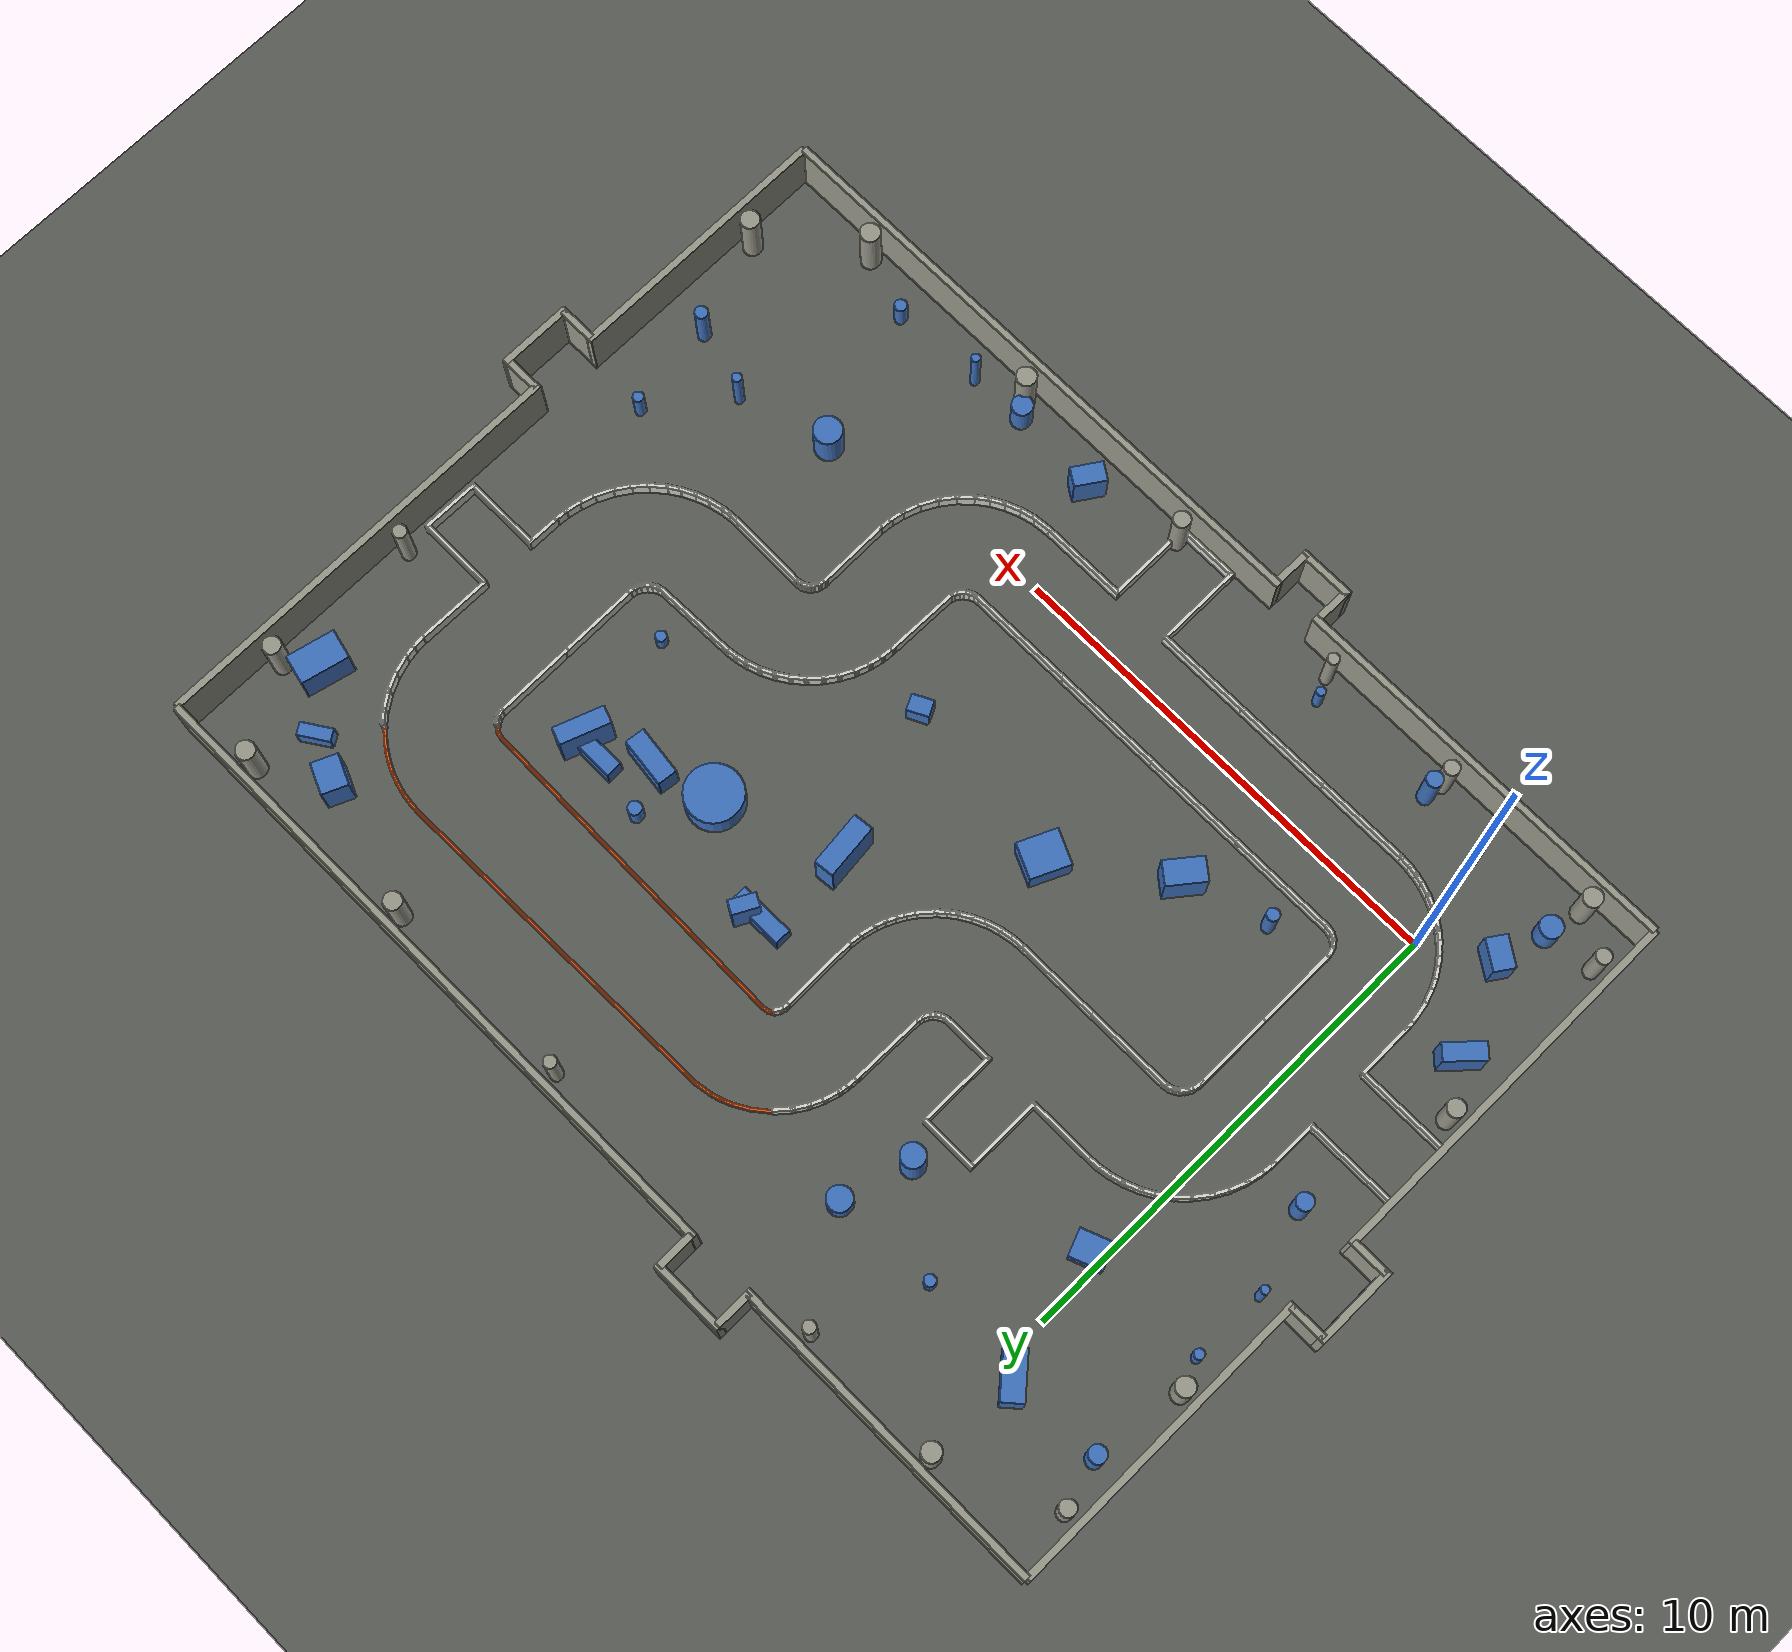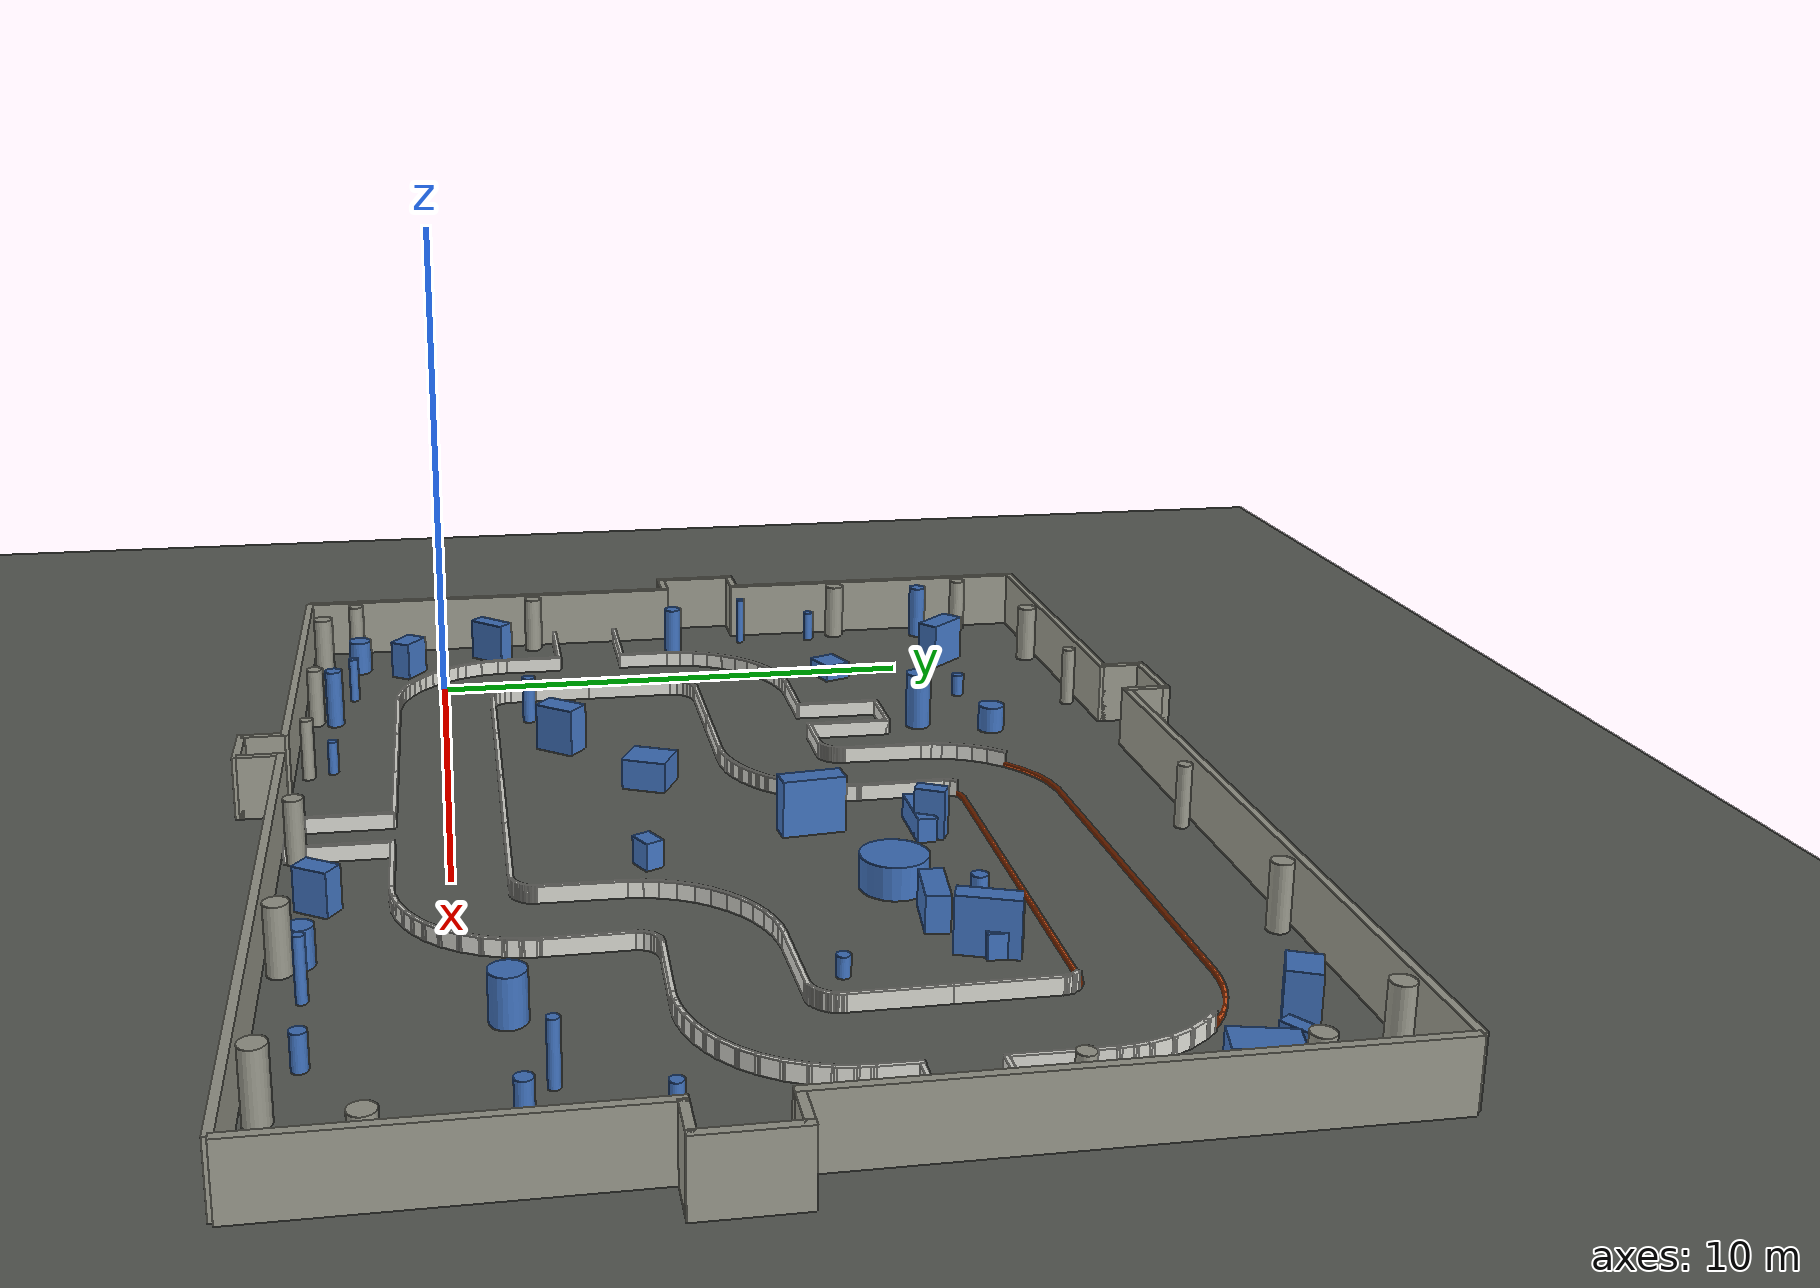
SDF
<?xml version="1.0" ?>
<sdf version="1.9">
  <!-- Generated by simulation/tools/generate_pose_dataset.py --install-gazebo-worlds from tools/pose_dataset/config/tracks.yaml (urban_grid). Do not edit by hand: change the YAML and regenerate. -->
  <world name="default">
    <physics name="default_physics" type="dart">
      <max_step_size>0.001</max_step_size>
      <real_time_factor>1.0</real_time_factor>
      <real_time_update_rate>1000.0</real_time_update_rate>
    </physics>
    <plugin filename="gz-sim-physics-system" name="gz::sim::systems::Physics" />
    <plugin filename="gz-sim-user-commands-system" name="gz::sim::systems::UserCommands" />
    <plugin filename="gz-sim-scene-broadcaster-system" name="gz::sim::systems::SceneBroadcaster" />
    <plugin filename="gz-sim-imu-system" name="gz::sim::systems::Imu" />
    <plugin filename="gz-sim-sensors-system" name="gz::sim::systems::Sensors">
      <render_engine>ogre2</render_engine>
    </plugin>
    <light type="directional" name="sun">
      <pose>0 0 10 0 0 0</pose>
      <diffuse>0.8 0.8 0.8 1</diffuse>
      <direction>-0.5 0.5 -1</direction>
      <cast_shadows>true</cast_shadows>
    </light>
    <model name="track_curb">
      <static>true</static>
      <pose>0 0 0 0 0 0</pose>
      <link name="curb_link">
        <collision name="left0_0_0_collision">
          <pose>15.271344 9.368254 0.035000 0.000000 0.000000 2.502777</pose>
          <geometry>
            <box>
              <size>0.189289 0.060000 0.070000</size>
            </box>
          </geometry>
        </collision>
        <visual name="left0_0_0_visual">
          <pose>15.271344 9.368254 0.035000 0.000000 0.000000 2.502777</pose>
          <geometry>
            <box>
              <size>0.189289 0.060000 0.070000</size>
            </box>
          </geometry>
          <material>
            <ambient>0.9 0.35 0.1 1</ambient>
            <diffuse>0.9 0.35 0.1 1</diffuse>
          </material>
        </visual>
        <collision name="left0_1_0_collision">
          <pose>15.157827 9.422156 0.035000 0.000000 0.000000 2.897335</pose>
          <geometry>
            <box>
              <size>0.187010 0.060000 0.070000</size>
            </box>
          </geometry>
        </collision>
        <visual name="left0_1_0_visual">
          <pose>15.157827 9.422156 0.035000 0.000000 0.000000 2.897335</pose>
          <geometry>
            <box>
              <size>0.187010 0.060000 0.070000</size>
            </box>
          </geometry>
          <material>
            <ambient>0.9 0.35 0.1 1</ambient>
            <diffuse>0.9 0.35 0.1 1</diffuse>
          </material>
        </visual>
        <collision name="left0_2_0_collision">
          <pose>13.877469 9.456981 0.035000 0.000000 0.000000 3.125621</pose>
          <geometry>
            <box>
              <size>2.497787 0.060000 0.070000</size>
            </box>
          </geometry>
        </collision>
        <visual name="left0_2_0_visual">
          <pose>13.877469 9.456981 0.035000 0.000000 0.000000 3.125621</pose>
          <geometry>
            <box>
              <size>2.497787 0.060000 0.070000</size>
            </box>
          </geometry>
          <material>
            <ambient>0.9 0.35 0.1 1</ambient>
            <diffuse>0.9 0.35 0.1 1</diffuse>
          </material>
        </visual>
        <collision name="left0_2_1_collision">
          <pose>11.439993 9.495915 0.035000 0.000000 0.000000 3.125621</pose>
          <geometry>
            <box>
              <size>2.497787 0.060000 0.070000</size>
            </box>
          </geometry>
        </collision>
        <visual name="left0_2_1_visual">
          <pose>11.439993 9.495915 0.035000 0.000000 0.000000 3.125621</pose>
          <geometry>
            <box>
              <size>2.497787 0.060000 0.070000</size>
            </box>
          </geometry>
          <material>
            <ambient>0.9 0.35 0.1 1</ambient>
            <diffuse>0.9 0.35 0.1 1</diffuse>
          </material>
        </visual>
        <collision name="left0_2_2_collision">
          <pose>9.002516 9.534850 0.035000 0.000000 0.000000 3.125621</pose>
          <geometry>
            <box>
              <size>2.497787 0.060000 0.070000</size>
            </box>
          </geometry>
        </collision>
        <visual name="left0_2_2_visual">
          <pose>9.002516 9.534850 0.035000 0.000000 0.000000 3.125621</pose>
          <geometry>
            <box>
              <size>2.497787 0.060000 0.070000</size>
            </box>
          </geometry>
          <material>
            <ambient>0.9 0.35 0.1 1</ambient>
            <diffuse>0.9 0.35 0.1 1</diffuse>
          </material>
        </visual>
        <collision name="left0_3_0_collision">
          <pose>7.711670 9.540087 0.035000 0.000000 0.000000 -2.946748</pose>
          <geometry>
            <box>
              <size>0.206997 0.060000 0.070000</size>
            </box>
          </geometry>
        </collision>
        <visual name="left0_3_0_visual">
          <pose>7.711670 9.540087 0.035000 0.000000 0.000000 -2.946748</pose>
          <geometry>
            <box>
              <size>0.206997 0.060000 0.070000</size>
            </box>
          </geometry>
          <material>
            <ambient>0.9 0.35 0.1 1</ambient>
            <diffuse>0.9 0.35 0.1 1</diffuse>
          </material>
        </visual>
        <collision name="left0_4_0_collision">
          <pose>7.600947 9.503579 0.035000 0.000000 0.000000 -2.618331</pose>
          <geometry>
            <box>
              <size>0.149162 0.060000 0.070000</size>
            </box>
          </geometry>
        </collision>
        <visual name="left0_4_0_visual">
          <pose>7.600947 9.503579 0.035000 0.000000 0.000000 -2.618331</pose>
          <geometry>
            <box>
              <size>0.149162 0.060000 0.070000</size>
            </box>
          </geometry>
          <material>
            <ambient>0.9 0.35 0.1 1</ambient>
            <diffuse>0.9 0.35 0.1 1</diffuse>
          </material>
        </visual>
        <collision name="left0_5_0_collision">
          <pose>7.551408 9.472403 0.035000 0.000000 0.000000 -2.457948</pose>
          <geometry>
            <box>
              <size>0.088178 0.060000 0.070000</size>
            </box>
          </geometry>
        </collision>
        <visual name="left0_5_0_visual">
          <pose>7.551408 9.472403 0.035000 0.000000 0.000000 -2.457948</pose>
          <geometry>
            <box>
              <size>0.088178 0.060000 0.070000</size>
            </box>
          </geometry>
          <material>
            <ambient>0.9 0.35 0.1 1</ambient>
            <diffuse>0.9 0.35 0.1 1</diffuse>
          </material>
        </visual>
        <collision name="left0_6_0_collision">
          <pose>7.542045 9.458009 0.035000 0.000000 0.000000 -1.294159</pose>
          <geometry>
            <box>
              <size>0.071423 0.060000 0.070000</size>
            </box>
          </geometry>
        </collision>
        <visual name="left0_6_0_visual">
          <pose>7.542045 9.458009 0.035000 0.000000 0.000000 -1.294159</pose>
          <geometry>
            <box>
              <size>0.071423 0.060000 0.070000</size>
            </box>
          </geometry>
          <material>
            <ambient>0.9 0.35 0.1 1</ambient>
            <diffuse>0.9 0.35 0.1 1</diffuse>
          </material>
        </visual>
        <collision name="right4_0_0_collision">
          <pose>16.748323 10.948203 0.035000 0.000000 0.000000 2.422302</pose>
          <geometry>
            <box>
              <size>0.272321 0.060000 0.070000</size>
            </box>
          </geometry>
        </collision>
        <visual name="right4_0_0_visual">
          <pose>16.748323 10.948203 0.035000 0.000000 0.000000 2.422302</pose>
          <geometry>
            <box>
              <size>0.272321 0.060000 0.070000</size>
            </box>
          </geometry>
          <material>
            <ambient>0.9 0.35 0.1 1</ambient>
            <diffuse>0.9 0.35 0.1 1</diffuse>
          </material>
        </visual>
        <collision name="right4_1_0_collision">
          <pose>16.568221 11.090692 0.035000 0.000000 0.000000 2.515127</pose>
          <geometry>
            <box>
              <size>0.307473 0.060000 0.070000</size>
            </box>
          </geometry>
        </collision>
        <visual name="right4_1_0_visual">
          <pose>16.568221 11.090692 0.035000 0.000000 0.000000 2.515127</pose>
          <geometry>
            <box>
              <size>0.307473 0.060000 0.070000</size>
            </box>
          </geometry>
          <material>
            <ambient>0.9 0.35 0.1 1</ambient>
            <diffuse>0.9 0.35 0.1 1</diffuse>
          </material>
        </visual>
        <collision name="right4_2_0_collision">
          <pose>16.361099 11.225360 0.035000 0.000000 0.000000 2.615095</pose>
          <geometry>
            <box>
              <size>0.307251 0.060000 0.070000</size>
            </box>
          </geometry>
        </collision>
        <visual name="right4_2_0_visual">
          <pose>16.361099 11.225360 0.035000 0.000000 0.000000 2.615095</pose>
          <geometry>
            <box>
              <size>0.307251 0.060000 0.070000</size>
            </box>
          </geometry>
          <material>
            <ambient>0.9 0.35 0.1 1</ambient>
            <diffuse>0.9 0.35 0.1 1</diffuse>
          </material>
        </visual>
        <collision name="right4_3_0_collision">
          <pose>16.141768 11.338582 0.035000 0.000000 0.000000 2.715063</pose>
          <geometry>
            <box>
              <size>0.307028 0.060000 0.070000</size>
            </box>
          </geometry>
        </collision>
        <visual name="right4_3_0_visual">
          <pose>16.141768 11.338582 0.035000 0.000000 0.000000 2.715063</pose>
          <geometry>
            <box>
              <size>0.307028 0.060000 0.070000</size>
            </box>
          </geometry>
          <material>
            <ambient>0.9 0.35 0.1 1</ambient>
            <diffuse>0.9 0.35 0.1 1</diffuse>
          </material>
        </visual>
        <collision name="right4_4_0_collision">
          <pose>15.929364 11.424333 0.035000 0.000000 0.000000 2.807892</pose>
          <geometry>
            <box>
              <size>0.271584 0.060000 0.070000</size>
            </box>
          </geometry>
        </collision>
        <visual name="right4_4_0_visual">
          <pose>15.929364 11.424333 0.035000 0.000000 0.000000 2.807892</pose>
          <geometry>
            <box>
              <size>0.271584 0.060000 0.070000</size>
            </box>
          </geometry>
          <material>
            <ambient>0.9 0.35 0.1 1</ambient>
            <diffuse>0.9 0.35 0.1 1</diffuse>
          </material>
        </visual>
        <collision name="right4_5_0_collision">
          <pose>15.709660 11.488399 0.035000 0.000000 0.000000 2.900717</pose>
          <geometry>
            <box>
              <size>0.306614 0.060000 0.070000</size>
            </box>
          </geometry>
        </collision>
        <visual name="right4_5_0_visual">
          <pose>15.709660 11.488399 0.035000 0.000000 0.000000 2.900717</pose>
          <geometry>
            <box>
              <size>0.306614 0.060000 0.070000</size>
            </box>
          </geometry>
          <material>
            <ambient>0.9 0.35 0.1 1</ambient>
            <diffuse>0.9 0.35 0.1 1</diffuse>
          </material>
        </visual>
        <collision name="right4_6_0_collision">
          <pose>15.467938 11.535116 0.035000 0.000000 0.000000 3.000685</pose>
          <geometry>
            <box>
              <size>0.306392 0.060000 0.070000</size>
            </box>
          </geometry>
        </collision>
        <visual name="right4_6_0_visual">
          <pose>15.467938 11.535116 0.035000 0.000000 0.000000 3.000685</pose>
          <geometry>
            <box>
              <size>0.306392 0.060000 0.070000</size>
            </box>
          </geometry>
          <material>
            <ambient>0.9 0.35 0.1 1</ambient>
            <diffuse>0.9 0.35 0.1 1</diffuse>
          </material>
        </visual>
        <collision name="right4_7_0_collision">
          <pose>15.224878 11.557452 0.035000 0.000000 0.000000 3.100041</pose>
          <geometry>
            <box>
              <size>0.302380 0.060000 0.070000</size>
            </box>
          </geometry>
        </collision>
        <visual name="right4_7_0_visual">
          <pose>15.224878 11.557452 0.035000 0.000000 0.000000 3.100041</pose>
          <geometry>
            <box>
              <size>0.302380 0.060000 0.070000</size>
            </box>
          </geometry>
          <material>
            <ambient>0.9 0.35 0.1 1</ambient>
            <diffuse>0.9 0.35 0.1 1</diffuse>
          </material>
        </visual>
        <collision name="right4_8_0_collision">
          <pose>13.857994 11.541765 0.035000 0.000000 0.000000 -3.124961</pose>
          <geometry>
            <box>
              <size>2.551941 0.060000 0.070000</size>
            </box>
          </geometry>
        </collision>
        <visual name="right4_8_0_visual">
          <pose>13.857994 11.541765 0.035000 0.000000 0.000000 -3.124961</pose>
          <geometry>
            <box>
              <size>2.551941 0.060000 0.070000</size>
            </box>
          </geometry>
          <material>
            <ambient>0.9 0.35 0.1 1</ambient>
            <diffuse>0.9 0.35 0.1 1</diffuse>
          </material>
        </visual>
        <collision name="right4_8_1_collision">
          <pose>11.366398 11.500322 0.035000 0.000000 0.000000 -3.124961</pose>
          <geometry>
            <box>
              <size>2.551941 0.060000 0.070000</size>
            </box>
          </geometry>
        </collision>
        <visual name="right4_8_1_visual">
          <pose>11.366398 11.500322 0.035000 0.000000 0.000000 -3.124961</pose>
          <geometry>
            <box>
              <size>2.551941 0.060000 0.070000</size>
            </box>
          </geometry>
          <material>
            <ambient>0.9 0.35 0.1 1</ambient>
            <diffuse>0.9 0.35 0.1 1</diffuse>
          </material>
        </visual>
        <collision name="right4_8_2_collision">
          <pose>8.874802 11.458879 0.035000 0.000000 0.000000 -3.124961</pose>
          <geometry>
            <box>
              <size>2.551941 0.060000 0.070000</size>
            </box>
          </geometry>
        </collision>
        <visual name="right4_8_2_visual">
          <pose>8.874802 11.458879 0.035000 0.000000 0.000000 -3.124961</pose>
          <geometry>
            <box>
              <size>2.551941 0.060000 0.070000</size>
            </box>
          </geometry>
          <material>
            <ambient>0.9 0.35 0.1 1</ambient>
            <diffuse>0.9 0.35 0.1 1</diffuse>
          </material>
        </visual>
        <collision name="right4_9_0_collision">
          <pose>7.443772 11.406488 0.035000 0.000000 0.000000 -2.972256</pose>
          <geometry>
            <box>
              <size>0.435840 0.060000 0.070000</size>
            </box>
          </geometry>
        </collision>
        <visual name="right4_9_0_visual">
          <pose>7.443772 11.406488 0.035000 0.000000 0.000000 -2.972256</pose>
          <geometry>
            <box>
              <size>0.435840 0.060000 0.070000</size>
            </box>
          </geometry>
          <material>
            <ambient>0.9 0.35 0.1 1</ambient>
            <diffuse>0.9 0.35 0.1 1</diffuse>
          </material>
        </visual>
        <collision name="right4_10_0_collision">
          <pose>7.160622 11.344637 0.035000 0.000000 0.000000 -2.842601</pose>
          <geometry>
            <box>
              <size>0.264927 0.060000 0.070000</size>
            </box>
          </geometry>
        </collision>
        <visual name="right4_10_0_visual">
          <pose>7.160622 11.344637 0.035000 0.000000 0.000000 -2.842601</pose>
          <geometry>
            <box>
              <size>0.264927 0.060000 0.070000</size>
            </box>
          </geometry>
          <material>
            <ambient>0.9 0.35 0.1 1</ambient>
            <diffuse>0.9 0.35 0.1 1</diffuse>
          </material>
        </visual>
        <collision name="right4_11_0_collision">
          <pose>6.968035 11.275485 0.035000 0.000000 0.000000 -2.751091</pose>
          <geometry>
            <box>
              <size>0.264754 0.060000 0.070000</size>
            </box>
          </geometry>
        </collision>
        <visual name="right4_11_0_visual">
          <pose>6.968035 11.275485 0.035000 0.000000 0.000000 -2.751091</pose>
          <geometry>
            <box>
              <size>0.264754 0.060000 0.070000</size>
            </box>
          </geometry>
          <material>
            <ambient>0.9 0.35 0.1 1</ambient>
            <diffuse>0.9 0.35 0.1 1</diffuse>
          </material>
        </visual>
        <collision name="right4_12_0_collision">
          <pose>6.710824 11.143423 0.035000 0.000000 0.000000 -2.621466</pose>
          <geometry>
            <box>
              <size>0.434623 0.060000 0.070000</size>
            </box>
          </geometry>
        </collision>
        <visual name="right4_12_0_visual">
          <pose>6.710824 11.143423 0.035000 0.000000 0.000000 -2.621466</pose>
          <geometry>
            <box>
              <size>0.434623 0.060000 0.070000</size>
            </box>
          </geometry>
          <material>
            <ambient>0.9 0.35 0.1 1</ambient>
            <diffuse>0.9 0.35 0.1 1</diffuse>
          </material>
        </visual>
        <collision name="right4_13_0_collision">
          <pose>6.376118 10.911111 0.035000 0.000000 0.000000 -2.461604</pose>
          <geometry>
            <box>
              <size>0.502823 0.060000 0.070000</size>
            </box>
          </geometry>
        </collision>
        <visual name="right4_13_0_visual">
          <pose>6.376118 10.911111 0.035000 0.000000 0.000000 -2.461604</pose>
          <geometry>
            <box>
              <size>0.502823 0.060000 0.070000</size>
            </box>
          </geometry>
          <material>
            <ambient>0.9 0.35 0.1 1</ambient>
            <diffuse>0.9 0.35 0.1 1</diffuse>
          </material>
        </visual>
      </link>
    </model>
    <model name="track_feature">
      <static>true</static>
      <pose>0 0 0 0 0 0</pose>
      <link name="feature_link">
        <collision name="feat_box_1_collision">
          <pose>12.639290 7.755865 0.330038 0.000000 0.000000 3.019790</pose>
          <geometry>
            <box>
              <size>1.058222 0.423274 0.660077</size>
            </box>
          </geometry>
        </collision>
        <visual name="feat_box_1_visual">
          <pose>12.639290 7.755865 0.330038 0.000000 0.000000 3.019790</pose>
          <geometry>
            <box>
              <size>1.058222 0.423274 0.660077</size>
            </box>
          </geometry>
          <material>
            <ambient>0.25 0.45 0.75 1</ambient>
            <diffuse>0.25 0.45 0.75 1</diffuse>
          </material>
        </visual>
        <collision name="feat_box_2_collision">
          <pose>0.279351 8.474213 0.176076 0.000000 0.000000 -1.197004</pose>
          <geometry>
            <box>
              <size>0.574998 0.694214 0.352152</size>
            </box>
          </geometry>
        </collision>
        <visual name="feat_box_2_visual">
          <pose>0.279351 8.474213 0.176076 0.000000 0.000000 -1.197004</pose>
          <geometry>
            <box>
              <size>0.574998 0.694214 0.352152</size>
            </box>
          </geometry>
          <material>
            <ambient>0.25 0.45 0.75 1</ambient>
            <diffuse>0.25 0.45 0.75 1</diffuse>
          </material>
        </visual>
        <collision name="feat_box_4_collision">
          <pose>10.784718 -2.181877 0.403142 0.000000 0.000000 2.555760</pose>
          <geometry>
            <box>
              <size>0.409974 0.674986 0.806284</size>
            </box>
          </geometry>
        </collision>
        <visual name="feat_box_4_visual">
          <pose>10.784718 -2.181877 0.403142 0.000000 0.000000 2.555760</pose>
          <geometry>
            <box>
              <size>0.409974 0.674986 0.806284</size>
            </box>
          </geometry>
          <material>
            <ambient>0.25 0.45 0.75 1</ambient>
            <diffuse>0.25 0.45 0.75 1</diffuse>
          </material>
        </visual>
        <collision name="feat_box_5_collision">
          <pose>16.598004 12.318466 0.431856 0.000000 0.000000 1.157170</pose>
          <geometry>
            <box>
              <size>0.557473 0.669891 0.863711</size>
            </box>
          </geometry>
        </collision>
        <visual name="feat_box_5_visual">
          <pose>16.598004 12.318466 0.431856 0.000000 0.000000 1.157170</pose>
          <geometry>
            <box>
              <size>0.557473 0.669891 0.863711</size>
            </box>
          </geometry>
          <material>
            <ambient>0.25 0.45 0.75 1</ambient>
            <diffuse>0.25 0.45 0.75 1</diffuse>
          </material>
        </visual>
        <collision name="feat_box_7_collision">
          <pose>3.940306 2.268397 0.467089 0.000000 0.000000 0.898028</pose>
          <geometry>
            <box>
              <size>0.836948 0.509742 0.934179</size>
            </box>
          </geometry>
        </collision>
        <visual name="feat_box_7_visual">
          <pose>3.940306 2.268397 0.467089 0.000000 0.000000 0.898028</pose>
          <geometry>
            <box>
              <size>0.836948 0.509742 0.934179</size>
            </box>
          </geometry>
          <material>
            <ambient>0.25 0.45 0.75 1</ambient>
            <diffuse>0.25 0.45 0.75 1</diffuse>
          </material>
        </visual>
        <collision name="feat_box_8_collision">
          <pose>-2.042347 1.082708 0.440779 0.000000 0.000000 0.819688</pose>
          <geometry>
            <box>
              <size>0.861431 0.366135 0.881558</size>
            </box>
          </geometry>
        </collision>
        <visual name="feat_box_8_visual">
          <pose>-2.042347 1.082708 0.440779 0.000000 0.000000 0.819688</pose>
          <geometry>
            <box>
              <size>0.861431 0.366135 0.881558</size>
            </box>
          </geometry>
          <material>
            <ambient>0.25 0.45 0.75 1</ambient>
            <diffuse>0.25 0.45 0.75 1</diffuse>
          </material>
        </visual>
        <collision name="feat_box_10_collision">
          <pose>9.809354 3.382879 0.254682 0.000000 0.000000 -1.108631</pose>
          <geometry>
            <box>
              <size>0.347329 0.461572 0.509363</size>
            </box>
          </geometry>
        </collision>
        <visual name="feat_box_10_visual">
          <pose>9.809354 3.382879 0.254682 0.000000 0.000000 -1.108631</pose>
          <geometry>
            <box>
              <size>0.347329 0.461572 0.509363</size>
            </box>
          </geometry>
          <material>
            <ambient>0.25 0.45 0.75 1</ambient>
            <diffuse>0.25 0.45 0.75 1</diffuse>
          </material>
        </visual>
        <collision name="feat_box_12_collision">
          <pose>-0.348791 11.138863 0.482820 0.000000 0.000000 -0.855922</pose>
          <geometry>
            <box>
              <size>0.993537 0.458591 0.965639</size>
            </box>
          </geometry>
        </collision>
        <visual name="feat_box_12_visual">
          <pose>-0.348791 11.138863 0.482820 0.000000 0.000000 -0.855922</pose>
          <geometry>
            <box>
              <size>0.993537 0.458591 0.965639</size>
            </box>
          </geometry>
          <material>
            <ambient>0.25 0.45 0.75 1</ambient>
            <diffuse>0.25 0.45 0.75 1</diffuse>
          </material>
        </visual>
        <collision name="feat_box_15_collision">
          <pose>6.080824 3.821925 0.294301 0.000000 0.000000 1.138007</pose>
          <geometry>
            <box>
              <size>0.858884 0.764687 0.588602</size>
            </box>
          </geometry>
        </collision>
        <visual name="feat_box_15_visual">
          <pose>6.080824 3.821925 0.294301 0.000000 0.000000 1.138007</pose>
          <geometry>
            <box>
              <size>0.858884 0.764687 0.588602</size>
            </box>
          </geometry>
          <material>
            <ambient>0.25 0.45 0.75 1</ambient>
            <diffuse>0.25 0.45 0.75 1</diffuse>
          </material>
        </visual>
        <collision name="feat_box_16_collision">
          <pose>-1.252297 -0.781731 0.395862 0.000000 0.000000 -2.167370</pose>
          <geometry>
            <box>
              <size>0.445202 0.665797 0.791723</size>
            </box>
          </geometry>
        </collision>
        <visual name="feat_box_16_visual">
          <pose>-1.252297 -0.781731 0.395862 0.000000 0.000000 -2.167370</pose>
          <geometry>
            <box>
              <size>0.445202 0.665797 0.791723</size>
            </box>
          </geometry>
          <material>
            <ambient>0.25 0.45 0.75 1</ambient>
            <diffuse>0.25 0.45 0.75 1</diffuse>
          </material>
        </visual>
        <collision name="feat_box_18_collision">
          <pose>8.748058 6.458404 0.530079 0.000000 0.000000 1.677954</pose>
          <geometry>
            <box>
              <size>1.177132 0.425119 1.060159</size>
            </box>
          </geometry>
        </collision>
        <visual name="feat_box_18_visual">
          <pose>8.748058 6.458404 0.530079 0.000000 0.000000 1.677954</pose>
          <geometry>
            <box>
              <size>1.177132 0.425119 1.060159</size>
            </box>
          </geometry>
          <material>
            <ambient>0.25 0.45 0.75 1</ambient>
            <diffuse>0.25 0.45 0.75 1</diffuse>
          </material>
        </visual>
        <collision name="feat_box_24_collision">
          <pose>9.284548 8.540532 0.457994 0.000000 0.000000 -0.491147</pose>
          <geometry>
            <box>
              <size>0.302029 0.562229 0.915989</size>
            </box>
          </geometry>
        </collision>
        <visual name="feat_box_24_visual">
          <pose>9.284548 8.540532 0.457994 0.000000 0.000000 -0.491147</pose>
          <geometry>
            <box>
              <size>0.302029 0.562229 0.915989</size>
            </box>
          </geometry>
          <material>
            <ambient>0.25 0.45 0.75 1</ambient>
            <diffuse>0.25 0.45 0.75 1</diffuse>
          </material>
        </visual>
        <collision name="feat_box_25_collision">
          <pose>18.518752 10.916348 0.397110 0.000000 0.000000 -1.805734</pose>
          <geometry>
            <box>
              <size>1.033357 0.635933 0.794219</size>
            </box>
          </geometry>
        </collision>
        <visual name="feat_box_25_visual">
          <pose>18.518752 10.916348 0.397110 0.000000 0.000000 -1.805734</pose>
          <geometry>
            <box>
              <size>1.033357 0.635933 0.794219</size>
            </box>
          </geometry>
          <material>
            <ambient>0.25 0.45 0.75 1</ambient>
            <diffuse>0.25 0.45 0.75 1</diffuse>
          </material>
        </visual>
        <collision name="feat_box_26_collision">
          <pose>13.912323 8.311295 0.505113 0.000000 0.000000 -1.924617</pose>
          <geometry>
            <box>
              <size>1.071921 0.373841 1.010225</size>
            </box>
          </geometry>
        </collision>
        <visual name="feat_box_26_visual">
          <pose>13.912323 8.311295 0.505113 0.000000 0.000000 -1.924617</pose>
          <geometry>
            <box>
              <size>1.071921 0.373841 1.010225</size>
            </box>
          </geometry>
          <material>
            <ambient>0.25 0.45 0.75 1</ambient>
            <diffuse>0.25 0.45 0.75 1</diffuse>
          </material>
        </visual>
        <collision name="feat_box_36_collision">
          <pose>17.582097 11.913602 0.199766 0.000000 0.000000 0.580317</pose>
          <geometry>
            <box>
              <size>0.678236 0.270606 0.399531</size>
            </box>
          </geometry>
        </collision>
        <visual name="feat_box_36_visual">
          <pose>17.582097 11.913602 0.199766 0.000000 0.000000 0.580317</pose>
          <geometry>
            <box>
              <size>0.678236 0.270606 0.399531</size>
            </box>
          </geometry>
          <material>
            <ambient>0.25 0.45 0.75 1</ambient>
            <diffuse>0.25 0.45 0.75 1</diffuse>
          </material>
        </visual>
        <collision name="landmark_1_collision">
          <pose>9.000000 8.400000 0.225000 0.000000 0.000000 0.000000</pose>
          <geometry>
            <box>
              <size>1.200000 0.350000 0.450000</size>
            </box>
          </geometry>
        </collision>
        <visual name="landmark_1_visual">
          <pose>9.000000 8.400000 0.225000 0.000000 0.000000 0.000000</pose>
          <geometry>
            <box>
              <size>1.200000 0.350000 0.450000</size>
            </box>
          </geometry>
          <material>
            <ambient>0.25 0.45 0.75 1</ambient>
            <diffuse>0.25 0.45 0.75 1</diffuse>
          </material>
        </visual>
        <collision name="landmark_2_collision">
          <pose>13.600000 8.400000 0.225000 0.000000 0.000000 0.000000</pose>
          <geometry>
            <box>
              <size>1.200000 0.350000 0.450000</size>
            </box>
          </geometry>
        </collision>
        <visual name="landmark_2_visual">
          <pose>13.600000 8.400000 0.225000 0.000000 0.000000 0.000000</pose>
          <geometry>
            <box>
              <size>1.200000 0.350000 0.450000</size>
            </box>
          </geometry>
          <material>
            <ambient>0.25 0.45 0.75 1</ambient>
            <diffuse>0.25 0.45 0.75 1</diffuse>
          </material>
        </visual>
        <collision name="feat_cyl_3_collision">
          <pose>4.600586 -2.188813 0.329742 0.000000 0.000000 0.000000</pose>
          <geometry>
            <cylinder>
              <radius>0.097606</radius>
              <length>0.659485</length>
            </cylinder>
          </geometry>
        </collision>
        <visual name="feat_cyl_3_visual">
          <pose>4.600586 -2.188813 0.329742 0.000000 0.000000 0.000000</pose>
          <geometry>
            <cylinder>
              <radius>0.097606</radius>
              <length>0.659485</length>
            </cylinder>
          </geometry>
          <material>
            <ambient>0.25 0.45 0.75 1</ambient>
            <diffuse>0.25 0.45 0.75 1</diffuse>
          </material>
        </visual>
        <collision name="feat_cyl_6_collision">
          <pose>16.949693 1.321475 0.538627 0.000000 0.000000 0.000000</pose>
          <geometry>
            <cylinder>
              <radius>0.100593</radius>
              <length>1.077254</length>
            </cylinder>
          </geometry>
        </collision>
        <visual name="feat_cyl_6_visual">
          <pose>16.949693 1.321475 0.538627 0.000000 0.000000 0.000000</pose>
          <geometry>
            <cylinder>
              <radius>0.100593</radius>
              <length>1.077254</length>
            </cylinder>
          </geometry>
          <material>
            <ambient>0.25 0.45 0.75 1</ambient>
            <diffuse>0.25 0.45 0.75 1</diffuse>
          </material>
        </visual>
        <collision name="feat_cyl_9_collision">
          <pose>-1.878088 5.219361 0.520360 0.000000 0.000000 0.000000</pose>
          <geometry>
            <cylinder>
              <radius>0.178732</radius>
              <length>1.040721</length>
            </cylinder>
          </geometry>
        </collision>
        <visual name="feat_cyl_9_visual">
          <pose>-1.878088 5.219361 0.520360 0.000000 0.000000 0.000000</pose>
          <geometry>
            <cylinder>
              <radius>0.178732</radius>
              <length>1.040721</length>
            </cylinder>
          </geometry>
          <material>
            <ambient>0.25 0.45 0.75 1</ambient>
            <diffuse>0.25 0.45 0.75 1</diffuse>
          </material>
        </visual>
        <collision name="feat_cyl_11_collision">
          <pose>12.732874 -2.332813 0.342586 0.000000 0.000000 0.000000</pose>
          <geometry>
            <cylinder>
              <radius>0.221294</radius>
              <length>0.685172</length>
            </cylinder>
          </geometry>
        </collision>
        <visual name="feat_cyl_11_visual">
          <pose>12.732874 -2.332813 0.342586 0.000000 0.000000 0.000000</pose>
          <geometry>
            <cylinder>
              <radius>0.221294</radius>
              <length>0.685172</length>
            </cylinder>
          </geometry>
          <material>
            <ambient>0.25 0.45 0.75 1</ambient>
            <diffuse>0.25 0.45 0.75 1</diffuse>
          </material>
        </visual>
        <collision name="feat_cyl_13_collision">
          <pose>14.347416 5.906214 0.182492 0.000000 0.000000 0.000000</pose>
          <geometry>
            <cylinder>
              <radius>0.117041</radius>
              <length>0.364984</length>
            </cylinder>
          </geometry>
        </collision>
        <visual name="feat_cyl_13_visual">
          <pose>14.347416 5.906214 0.182492 0.000000 0.000000 0.000000</pose>
          <geometry>
            <cylinder>
              <radius>0.117041</radius>
              <length>0.364984</length>
            </cylinder>
          </geometry>
          <material>
            <ambient>0.25 0.45 0.75 1</ambient>
            <diffuse>0.25 0.45 0.75 1</diffuse>
          </material>
        </visual>
        <collision name="feat_cyl_14_collision">
          <pose>15.945334 -2.171955 0.306854 0.000000 0.000000 0.000000</pose>
          <geometry>
            <cylinder>
              <radius>0.130943</radius>
              <length>0.613709</length>
            </cylinder>
          </geometry>
        </collision>
        <visual name="feat_cyl_14_visual">
          <pose>15.945334 -2.171955 0.306854 0.000000 0.000000 0.000000</pose>
          <geometry>
            <cylinder>
              <radius>0.130943</radius>
              <length>0.613709</length>
            </cylinder>
          </geometry>
          <material>
            <ambient>0.25 0.45 0.75 1</ambient>
            <diffuse>0.25 0.45 0.75 1</diffuse>
          </material>
        </visual>
        <collision name="feat_cyl_17_collision">
          <pose>1.937383 10.968439 0.222637 0.000000 0.000000 0.000000</pose>
          <geometry>
            <cylinder>
              <radius>0.121931</radius>
              <length>0.445275</length>
            </cylinder>
          </geometry>
        </collision>
        <visual name="feat_cyl_17_visual">
          <pose>1.937383 10.968439 0.222637 0.000000 0.000000 0.000000</pose>
          <geometry>
            <cylinder>
              <radius>0.121931</radius>
              <length>0.445275</length>
            </cylinder>
          </geometry>
          <material>
            <ambient>0.25 0.45 0.75 1</ambient>
            <diffuse>0.25 0.45 0.75 1</diffuse>
          </material>
        </visual>
        <collision name="feat_cyl_19_collision">
          <pose>-1.582676 -1.849337 0.356050 0.000000 0.000000 0.000000</pose>
          <geometry>
            <cylinder>
              <radius>0.236233</radius>
              <length>0.712101</length>
            </cylinder>
          </geometry>
        </collision>
        <visual name="feat_cyl_19_visual">
          <pose>-1.582676 -1.849337 0.356050 0.000000 0.000000 0.000000</pose>
          <geometry>
            <cylinder>
              <radius>0.236233</radius>
              <length>0.712101</length>
            </cylinder>
          </geometry>
          <material>
            <ambient>0.25 0.45 0.75 1</ambient>
            <diffuse>0.25 0.45 0.75 1</diffuse>
          </material>
        </visual>
        <collision name="feat_cyl_20_collision">
          <pose>18.152635 2.872327 0.339768 0.000000 0.000000 0.000000</pose>
          <geometry>
            <cylinder>
              <radius>0.114547</radius>
              <length>0.679537</length>
            </cylinder>
          </geometry>
        </collision>
        <visual name="feat_cyl_20_visual">
          <pose>18.152635 2.872327 0.339768 0.000000 0.000000 0.000000</pose>
          <geometry>
            <cylinder>
              <radius>0.114547</radius>
              <length>0.679537</length>
            </cylinder>
          </geometry>
          <material>
            <ambient>0.25 0.45 0.75 1</ambient>
            <diffuse>0.25 0.45 0.75 1</diffuse>
          </material>
        </visual>
        <collision name="feat_cyl_21_collision">
          <pose>4.143815 11.094112 0.264145 0.000000 0.000000 0.000000</pose>
          <geometry>
            <cylinder>
              <radius>0.259900</radius>
              <length>0.528291</length>
            </cylinder>
          </geometry>
        </collision>
        <visual name="feat_cyl_21_visual">
          <pose>4.143815 11.094112 0.264145 0.000000 0.000000 0.000000</pose>
          <geometry>
            <cylinder>
              <radius>0.259900</radius>
              <length>0.528291</length>
            </cylinder>
          </geometry>
          <material>
            <ambient>0.25 0.45 0.75 1</ambient>
            <diffuse>0.25 0.45 0.75 1</diffuse>
          </material>
        </visual>
        <collision name="feat_cyl_22_collision">
          <pose>12.156014 8.649866 0.262049 0.000000 0.000000 0.000000</pose>
          <geometry>
            <cylinder>
              <radius>0.145643</radius>
              <length>0.524097</length>
            </cylinder>
          </geometry>
        </collision>
        <visual name="feat_cyl_22_visual">
          <pose>12.156014 8.649866 0.262049 0.000000 0.000000 0.000000</pose>
          <geometry>
            <cylinder>
              <radius>0.145643</radius>
              <length>0.524097</length>
            </cylinder>
          </geometry>
          <material>
            <ambient>0.25 0.45 0.75 1</ambient>
            <diffuse>0.25 0.45 0.75 1</diffuse>
          </material>
        </visual>
        <collision name="feat_cyl_23_collision">
          <pose>3.691648 9.659883 0.569830 0.000000 0.000000 0.000000</pose>
          <geometry>
            <cylinder>
              <radius>0.249498</radius>
              <length>1.139660</length>
            </cylinder>
          </geometry>
        </collision>
        <visual name="feat_cyl_23_visual">
          <pose>3.691648 9.659883 0.569830 0.000000 0.000000 0.000000</pose>
          <geometry>
            <cylinder>
              <radius>0.249498</radius>
              <length>1.139660</length>
            </cylinder>
          </geometry>
          <material>
            <ambient>0.25 0.45 0.75 1</ambient>
            <diffuse>0.25 0.45 0.75 1</diffuse>
          </material>
        </visual>
        <collision name="feat_cyl_27_collision">
          <pose>-2.460548 6.876080 0.508994 0.000000 0.000000 0.000000</pose>
          <geometry>
            <cylinder>
              <radius>0.088500</radius>
              <length>1.017987</length>
            </cylinder>
          </geometry>
        </collision>
        <visual name="feat_cyl_27_visual">
          <pose>-2.460548 6.876080 0.508994 0.000000 0.000000 0.000000</pose>
          <geometry>
            <cylinder>
              <radius>0.088500</radius>
              <length>1.017987</length>
            </cylinder>
          </geometry>
          <material>
            <ambient>0.25 0.45 0.75 1</ambient>
            <diffuse>0.25 0.45 0.75 1</diffuse>
          </material>
        </visual>
        <collision name="feat_cyl_28_collision">
          <pose>2.207614 1.719554 0.474230 0.000000 0.000000 0.000000</pose>
          <geometry>
            <cylinder>
              <radius>0.133858</radius>
              <length>0.948460</length>
            </cylinder>
          </geometry>
        </collision>
        <visual name="feat_cyl_28_visual">
          <pose>2.207614 1.719554 0.474230 0.000000 0.000000 0.000000</pose>
          <geometry>
            <cylinder>
              <radius>0.133858</radius>
              <length>0.948460</length>
            </cylinder>
          </geometry>
          <material>
            <ambient>0.25 0.45 0.75 1</ambient>
            <diffuse>0.25 0.45 0.75 1</diffuse>
          </material>
        </visual>
        <collision name="feat_cyl_29_collision">
          <pose>18.440880 0.855160 0.529392 0.000000 0.000000 0.000000</pose>
          <geometry>
            <cylinder>
              <radius>0.137709</radius>
              <length>1.058784</length>
            </cylinder>
          </geometry>
        </collision>
        <visual name="feat_cyl_29_visual">
          <pose>18.440880 0.855160 0.529392 0.000000 0.000000 0.000000</pose>
          <geometry>
            <cylinder>
              <radius>0.137709</radius>
              <length>1.058784</length>
            </cylinder>
          </geometry>
          <material>
            <ambient>0.25 0.45 0.75 1</ambient>
            <diffuse>0.25 0.45 0.75 1</diffuse>
          </material>
        </visual>
        <collision name="feat_cyl_30_collision">
          <pose>-2.415133 8.489460 0.323254 0.000000 0.000000 0.000000</pose>
          <geometry>
            <cylinder>
              <radius>0.106670</radius>
              <length>0.646509</length>
            </cylinder>
          </geometry>
        </collision>
        <visual name="feat_cyl_30_visual">
          <pose>-2.415133 8.489460 0.323254 0.000000 0.000000 0.000000</pose>
          <geometry>
            <cylinder>
              <radius>0.106670</radius>
              <length>0.646509</length>
            </cylinder>
          </geometry>
          <material>
            <ambient>0.25 0.45 0.75 1</ambient>
            <diffuse>0.25 0.45 0.75 1</diffuse>
          </material>
        </visual>
        <collision name="feat_cyl_31_collision">
          <pose>13.951009 -2.258323 0.556350 0.000000 0.000000 0.000000</pose>
          <geometry>
            <cylinder>
              <radius>0.095429</radius>
              <length>1.112701</length>
            </cylinder>
          </geometry>
        </collision>
        <visual name="feat_cyl_31_visual">
          <pose>13.951009 -2.258323 0.556350 0.000000 0.000000 0.000000</pose>
          <geometry>
            <cylinder>
              <radius>0.095429</radius>
              <length>1.112701</length>
            </cylinder>
          </geometry>
          <material>
            <ambient>0.25 0.45 0.75 1</ambient>
            <diffuse>0.25 0.45 0.75 1</diffuse>
          </material>
        </visual>
        <collision name="feat_cyl_32_collision">
          <pose>14.985311 0.772652 0.421128 0.000000 0.000000 0.000000</pose>
          <geometry>
            <cylinder>
              <radius>0.301136</radius>
              <length>0.842256</length>
            </cylinder>
          </geometry>
        </collision>
        <visual name="feat_cyl_32_visual">
          <pose>14.985311 0.772652 0.421128 0.000000 0.000000 0.000000</pose>
          <geometry>
            <cylinder>
              <radius>0.301136</radius>
              <length>0.842256</length>
            </cylinder>
          </geometry>
          <material>
            <ambient>0.25 0.45 0.75 1</ambient>
            <diffuse>0.25 0.45 0.75 1</diffuse>
          </material>
        </visual>
        <collision name="feat_cyl_33_collision">
          <pose>1.848057 -2.266543 0.588026 0.000000 0.000000 0.000000</pose>
          <geometry>
            <cylinder>
              <radius>0.170135</radius>
              <length>1.176052</length>
            </cylinder>
          </geometry>
        </collision>
        <visual name="feat_cyl_33_visual">
          <pose>1.848057 -2.266543 0.588026 0.000000 0.000000 0.000000</pose>
          <geometry>
            <cylinder>
              <radius>0.170135</radius>
              <length>1.176052</length>
            </cylinder>
          </geometry>
          <material>
            <ambient>0.25 0.45 0.75 1</ambient>
            <diffuse>0.25 0.45 0.75 1</diffuse>
          </material>
        </visual>
        <collision name="feat_cyl_34_collision">
          <pose>-2.371496 11.095588 0.579647 0.000000 0.000000 0.000000</pose>
          <geometry>
            <cylinder>
              <radius>0.181868</radius>
              <length>1.159294</length>
            </cylinder>
          </geometry>
        </collision>
        <visual name="feat_cyl_34_visual">
          <pose>-2.371496 11.095588 0.579647 0.000000 0.000000 0.000000</pose>
          <geometry>
            <cylinder>
              <radius>0.181868</radius>
              <length>1.159294</length>
            </cylinder>
          </geometry>
          <material>
            <ambient>0.25 0.45 0.75 1</ambient>
            <diffuse>0.25 0.45 0.75 1</diffuse>
          </material>
        </visual>
        <collision name="feat_cyl_35_collision">
          <pose>0.351594 -1.922661 0.463418 0.000000 0.000000 0.000000</pose>
          <geometry>
            <cylinder>
              <radius>0.094337</radius>
              <length>0.926837</length>
            </cylinder>
          </geometry>
        </collision>
        <visual name="feat_cyl_35_visual">
          <pose>0.351594 -1.922661 0.463418 0.000000 0.000000 0.000000</pose>
          <geometry>
            <cylinder>
              <radius>0.094337</radius>
              <length>0.926837</length>
            </cylinder>
          </geometry>
          <material>
            <ambient>0.25 0.45 0.75 1</ambient>
            <diffuse>0.25 0.45 0.75 1</diffuse>
          </material>
        </visual>
        <collision name="landmark_0_collision">
          <pose>11.300000 7.400000 0.300000 0.000000 0.000000 0.000000</pose>
          <geometry>
            <cylinder>
              <radius>0.600000</radius>
              <length>0.600000</length>
            </cylinder>
          </geometry>
        </collision>
        <visual name="landmark_0_visual">
          <pose>11.300000 7.400000 0.300000 0.000000 0.000000 0.000000</pose>
          <geometry>
            <cylinder>
              <radius>0.600000</radius>
              <length>0.600000</length>
            </cylinder>
          </geometry>
          <material>
            <ambient>0.25 0.45 0.75 1</ambient>
            <diffuse>0.25 0.45 0.75 1</diffuse>
          </material>
        </visual>
      </link>
    </model>
    <model name="track_ground">
      <static>true</static>
      <pose>0 0 0 0 0 0</pose>
      <link name="ground_link">
        <collision name="ground_collision">
          <pose>8.363762 5.082239 -0.025000 0.000000 0.000000 0.000000</pose>
          <geometry>
            <box>
              <size>80.000000 80.000000 0.050000</size>
            </box>
          </geometry>
          <surface>
            <friction>
              <ode>
                <mu>1.2</mu>
                <mu2>1.2</mu2>
              </ode>
            </friction>
            <contact>
              <ode>
                <kp>100000.0</kp>
                <kd>10.0</kd>
              </ode>
            </contact>
          </surface>
        </collision>
        <visual name="ground_visual">
          <pose>8.363762 5.082239 -0.025000 0.000000 0.000000 0.000000</pose>
          <geometry>
            <box>
              <size>80.000000 80.000000 0.050000</size>
            </box>
          </geometry>
          <material>
            <ambient>0.35 0.36 0.34 1</ambient>
            <diffuse>0.35 0.36 0.34 1</diffuse>
          </material>
        </visual>
      </link>
    </model>
    <model name="track_room">
      <static>true</static>
      <pose>0 0 0 0 0 0</pose>
      <link name="room_link">
        <collision name="hall_0_0_collision">
          <pose>1.310878 -3.000000 0.600000 0.000000 0.000000 0.000000</pose>
          <geometry>
            <box>
              <size>8.621756 0.150000 1.200000</size>
            </box>
          </geometry>
        </collision>
        <visual name="hall_0_0_visual">
          <pose>1.310878 -3.000000 0.600000 0.000000 0.000000 0.000000</pose>
          <geometry>
            <box>
              <size>8.621756 0.150000 1.200000</size>
            </box>
          </geometry>
          <material>
            <ambient>0.6 0.6 0.55 1</ambient>
            <diffuse>0.6 0.6 0.55 1</diffuse>
          </material>
        </visual>
        <collision name="hall_0_95_collision">
          <pose>13.017378 -3.000000 0.600000 0.000000 0.000000 0.000000</pose>
          <geometry>
            <box>
              <size>12.965245 0.150000 1.200000</size>
            </box>
          </geometry>
        </collision>
        <visual name="hall_0_95_visual">
          <pose>13.017378 -3.000000 0.600000 0.000000 0.000000 0.000000</pose>
          <geometry>
            <box>
              <size>12.965245 0.150000 1.200000</size>
            </box>
          </geometry>
          <material>
            <ambient>0.6 0.6 0.55 1</ambient>
            <diffuse>0.6 0.6 0.55 1</diffuse>
          </material>
        </visual>
        <collision name="hall_niche_0_collision">
          <pose>6.078255 -3.800000 0.600000 0.000000 0.000000 0.000000</pose>
          <geometry>
            <box>
              <size>1.213000 0.150000 1.200000</size>
            </box>
          </geometry>
        </collision>
        <visual name="hall_niche_0_visual">
          <pose>6.078255 -3.800000 0.600000 0.000000 0.000000 0.000000</pose>
          <geometry>
            <box>
              <size>1.213000 0.150000 1.200000</size>
            </box>
          </geometry>
          <material>
            <ambient>0.6 0.6 0.55 1</ambient>
            <diffuse>0.6 0.6 0.55 1</diffuse>
          </material>
        </visual>
        <collision name="hall_jamb_0_-1_collision">
          <pose>5.546756 -3.400000 0.600000 0.000000 0.000000 0.000000</pose>
          <geometry>
            <box>
              <size>0.150000 0.800000 1.200000</size>
            </box>
          </geometry>
        </collision>
        <visual name="hall_jamb_0_-1_visual">
          <pose>5.546756 -3.400000 0.600000 0.000000 0.000000 0.000000</pose>
          <geometry>
            <box>
              <size>0.150000 0.800000 1.200000</size>
            </box>
          </geometry>
          <material>
            <ambient>0.6 0.6 0.55 1</ambient>
            <diffuse>0.6 0.6 0.55 1</diffuse>
          </material>
        </visual>
        <collision name="hall_jamb_0_1_collision">
          <pose>6.609755 -3.400000 0.600000 0.000000 0.000000 0.000000</pose>
          <geometry>
            <box>
              <size>0.150000 0.800000 1.200000</size>
            </box>
          </geometry>
        </collision>
        <visual name="hall_jamb_0_1_visual">
          <pose>6.609755 -3.400000 0.600000 0.000000 0.000000 0.000000</pose>
          <geometry>
            <box>
              <size>0.150000 0.800000 1.200000</size>
            </box>
          </geometry>
          <material>
            <ambient>0.6 0.6 0.55 1</ambient>
            <diffuse>0.6 0.6 0.55 1</diffuse>
          </material>
        </visual>
        <collision name="hall_1_0_collision">
          <pose>19.500000 -0.068882 0.600000 0.000000 0.000000 1.570796</pose>
          <geometry>
            <box>
              <size>5.862236 0.150000 1.200000</size>
            </box>
          </geometry>
        </collision>
        <visual name="hall_1_0_visual">
          <pose>19.500000 -0.068882 0.600000 0.000000 0.000000 1.570796</pose>
          <geometry>
            <box>
              <size>5.862236 0.150000 1.200000</size>
            </box>
          </geometry>
          <material>
            <ambient>0.6 0.6 0.55 1</ambient>
            <diffuse>0.6 0.6 0.55 1</diffuse>
          </material>
        </visual>
        <collision name="hall_1_71_collision">
          <pose>19.500000 8.844853 0.600000 0.000000 0.000000 1.570796</pose>
          <geometry>
            <box>
              <size>9.310294 0.150000 1.200000</size>
            </box>
          </geometry>
        </collision>
        <visual name="hall_1_71_visual">
          <pose>19.500000 8.844853 0.600000 0.000000 0.000000 1.570796</pose>
          <geometry>
            <box>
              <size>9.310294 0.150000 1.200000</size>
            </box>
          </geometry>
          <material>
            <ambient>0.6 0.6 0.55 1</ambient>
            <diffuse>0.6 0.6 0.55 1</diffuse>
          </material>
        </visual>
        <collision name="hall_niche_1_collision">
          <pose>20.300000 3.525971 0.600000 0.000000 0.000000 1.570796</pose>
          <geometry>
            <box>
              <size>1.627470 0.150000 1.200000</size>
            </box>
          </geometry>
        </collision>
        <visual name="hall_niche_1_visual">
          <pose>20.300000 3.525971 0.600000 0.000000 0.000000 1.570796</pose>
          <geometry>
            <box>
              <size>1.627470 0.150000 1.200000</size>
            </box>
          </geometry>
          <material>
            <ambient>0.6 0.6 0.55 1</ambient>
            <diffuse>0.6 0.6 0.55 1</diffuse>
          </material>
        </visual>
        <collision name="hall_jamb_1_-1_collision">
          <pose>19.900000 2.787236 0.600000 0.000000 0.000000 1.570796</pose>
          <geometry>
            <box>
              <size>0.150000 0.800000 1.200000</size>
            </box>
          </geometry>
        </collision>
        <visual name="hall_jamb_1_-1_visual">
          <pose>19.900000 2.787236 0.600000 0.000000 0.000000 1.570796</pose>
          <geometry>
            <box>
              <size>0.150000 0.800000 1.200000</size>
            </box>
          </geometry>
          <material>
            <ambient>0.6 0.6 0.55 1</ambient>
            <diffuse>0.6 0.6 0.55 1</diffuse>
          </material>
        </visual>
        <collision name="hall_jamb_1_1_collision">
          <pose>19.900000 4.264706 0.600000 0.000000 0.000000 1.570796</pose>
          <geometry>
            <box>
              <size>0.150000 0.800000 1.200000</size>
            </box>
          </geometry>
        </collision>
        <visual name="hall_jamb_1_1_visual">
          <pose>19.900000 4.264706 0.600000 0.000000 0.000000 1.570796</pose>
          <geometry>
            <box>
              <size>0.150000 0.800000 1.200000</size>
            </box>
          </geometry>
          <material>
            <ambient>0.6 0.6 0.55 1</ambient>
            <diffuse>0.6 0.6 0.55 1</diffuse>
          </material>
        </visual>
        <collision name="hall_2_0_collision">
          <pose>12.443840 13.500000 0.600000 0.000000 0.000000 3.141593</pose>
          <geometry>
            <box>
              <size>14.112320 0.150000 1.200000</size>
            </box>
          </geometry>
        </collision>
        <visual name="hall_2_0_visual">
          <pose>12.443840 13.500000 0.600000 0.000000 0.000000 3.141593</pose>
          <geometry>
            <box>
              <size>14.112320 0.150000 1.200000</size>
            </box>
          </geometry>
          <material>
            <ambient>0.6 0.6 0.55 1</ambient>
            <diffuse>0.6 0.6 0.55 1</diffuse>
          </material>
        </visual>
        <collision name="hall_2_154_collision">
          <pose>0.525991 13.500000 0.600000 0.000000 0.000000 3.141593</pose>
          <geometry>
            <box>
              <size>7.051982 0.150000 1.200000</size>
            </box>
          </geometry>
        </collision>
        <visual name="hall_2_154_visual">
          <pose>0.525991 13.500000 0.600000 0.000000 0.000000 3.141593</pose>
          <geometry>
            <box>
              <size>7.051982 0.150000 1.200000</size>
            </box>
          </geometry>
          <material>
            <ambient>0.6 0.6 0.55 1</ambient>
            <diffuse>0.6 0.6 0.55 1</diffuse>
          </material>
        </visual>
        <collision name="hall_niche_2_collision">
          <pose>4.719831 14.300000 0.600000 0.000000 0.000000 3.141593</pose>
          <geometry>
            <box>
              <size>1.635698 0.150000 1.200000</size>
            </box>
          </geometry>
        </collision>
        <visual name="hall_niche_2_visual">
          <pose>4.719831 14.300000 0.600000 0.000000 0.000000 3.141593</pose>
          <geometry>
            <box>
              <size>1.635698 0.150000 1.200000</size>
            </box>
          </geometry>
          <material>
            <ambient>0.6 0.6 0.55 1</ambient>
            <diffuse>0.6 0.6 0.55 1</diffuse>
          </material>
        </visual>
        <collision name="hall_jamb_2_-1_collision">
          <pose>5.462680 13.900000 0.600000 0.000000 0.000000 3.141593</pose>
          <geometry>
            <box>
              <size>0.150000 0.800000 1.200000</size>
            </box>
          </geometry>
        </collision>
        <visual name="hall_jamb_2_-1_visual">
          <pose>5.462680 13.900000 0.600000 0.000000 0.000000 3.141593</pose>
          <geometry>
            <box>
              <size>0.150000 0.800000 1.200000</size>
            </box>
          </geometry>
          <material>
            <ambient>0.6 0.6 0.55 1</ambient>
            <diffuse>0.6 0.6 0.55 1</diffuse>
          </material>
        </visual>
        <collision name="hall_jamb_2_1_collision">
          <pose>3.976982 13.900000 0.600000 0.000000 0.000000 3.141593</pose>
          <geometry>
            <box>
              <size>0.150000 0.800000 1.200000</size>
            </box>
          </geometry>
        </collision>
        <visual name="hall_jamb_2_1_visual">
          <pose>3.976982 13.900000 0.600000 0.000000 0.000000 3.141593</pose>
          <geometry>
            <box>
              <size>0.150000 0.800000 1.200000</size>
            </box>
          </geometry>
          <material>
            <ambient>0.6 0.6 0.55 1</ambient>
            <diffuse>0.6 0.6 0.55 1</diffuse>
          </material>
        </visual>
        <collision name="hall_3_0_collision">
          <pose>-3.000000 10.110790 0.600000 0.000000 0.000000 -1.570796</pose>
          <geometry>
            <box>
              <size>6.778420 0.150000 1.200000</size>
            </box>
          </geometry>
        </collision>
        <visual name="hall_3_0_visual">
          <pose>-3.000000 10.110790 0.600000 0.000000 0.000000 -1.570796</pose>
          <geometry>
            <box>
              <size>6.778420 0.150000 1.200000</size>
            </box>
          </geometry>
          <material>
            <ambient>0.6 0.6 0.55 1</ambient>
            <diffuse>0.6 0.6 0.55 1</diffuse>
          </material>
        </visual>
        <collision name="hall_3_82_collision">
          <pose>-3.000000 1.117884 0.600000 0.000000 0.000000 -1.570796</pose>
          <geometry>
            <box>
              <size>8.235767 0.150000 1.200000</size>
            </box>
          </geometry>
        </collision>
        <visual name="hall_3_82_visual">
          <pose>-3.000000 1.117884 0.600000 0.000000 0.000000 -1.570796</pose>
          <geometry>
            <box>
              <size>8.235767 0.150000 1.200000</size>
            </box>
          </geometry>
          <material>
            <ambient>0.6 0.6 0.55 1</ambient>
            <diffuse>0.6 0.6 0.55 1</diffuse>
          </material>
        </visual>
        <collision name="hall_niche_3_collision">
          <pose>-3.800000 5.978674 0.600000 0.000000 0.000000 -1.570796</pose>
          <geometry>
            <box>
              <size>1.785813 0.150000 1.200000</size>
            </box>
          </geometry>
        </collision>
        <visual name="hall_niche_3_visual">
          <pose>-3.800000 5.978674 0.600000 0.000000 0.000000 -1.570796</pose>
          <geometry>
            <box>
              <size>1.785813 0.150000 1.200000</size>
            </box>
          </geometry>
          <material>
            <ambient>0.6 0.6 0.55 1</ambient>
            <diffuse>0.6 0.6 0.55 1</diffuse>
          </material>
        </visual>
        <collision name="hall_jamb_3_-1_collision">
          <pose>-3.400000 6.796580 0.600000 0.000000 0.000000 -1.570796</pose>
          <geometry>
            <box>
              <size>0.150000 0.800000 1.200000</size>
            </box>
          </geometry>
        </collision>
        <visual name="hall_jamb_3_-1_visual">
          <pose>-3.400000 6.796580 0.600000 0.000000 0.000000 -1.570796</pose>
          <geometry>
            <box>
              <size>0.150000 0.800000 1.200000</size>
            </box>
          </geometry>
          <material>
            <ambient>0.6 0.6 0.55 1</ambient>
            <diffuse>0.6 0.6 0.55 1</diffuse>
          </material>
        </visual>
        <collision name="hall_jamb_3_1_collision">
          <pose>-3.400000 5.160767 0.600000 0.000000 0.000000 -1.570796</pose>
          <geometry>
            <box>
              <size>0.150000 0.800000 1.200000</size>
            </box>
          </geometry>
        </collision>
        <visual name="hall_jamb_3_1_visual">
          <pose>-3.400000 5.160767 0.600000 0.000000 0.000000 -1.570796</pose>
          <geometry>
            <box>
              <size>0.150000 0.800000 1.200000</size>
            </box>
          </geometry>
          <material>
            <ambient>0.6 0.6 0.55 1</ambient>
            <diffuse>0.6 0.6 0.55 1</diffuse>
          </material>
        </visual>
        <collision name="column_0_12_collision">
          <pose>-1.760781 -2.650000 0.600000 0.000000 0.000000 0.000000</pose>
          <geometry>
            <cylinder>
              <radius>0.200121</radius>
              <length>1.200000</length>
            </cylinder>
          </geometry>
        </collision>
        <visual name="column_0_12_visual">
          <pose>-1.760781 -2.650000 0.600000 0.000000 0.000000 0.000000</pose>
          <geometry>
            <cylinder>
              <radius>0.200121</radius>
              <length>1.200000</length>
            </cylinder>
          </geometry>
          <material>
            <ambient>0.6 0.6 0.55 1</ambient>
            <diffuse>0.6 0.6 0.55 1</diffuse>
          </material>
        </visual>
        <collision name="column_0_47_collision">
          <pose>1.769769 -2.650000 0.600000 0.000000 0.000000 0.000000</pose>
          <geometry>
            <cylinder>
              <radius>0.160983</radius>
              <length>1.200000</length>
            </cylinder>
          </geometry>
        </collision>
        <visual name="column_0_47_visual">
          <pose>1.769769 -2.650000 0.600000 0.000000 0.000000 0.000000</pose>
          <geometry>
            <cylinder>
              <radius>0.160983</radius>
              <length>1.200000</length>
            </cylinder>
          </geometry>
          <material>
            <ambient>0.6 0.6 0.55 1</ambient>
            <diffuse>0.6 0.6 0.55 1</diffuse>
          </material>
        </visual>
        <collision name="column_0_78_collision">
          <pose>4.801967 -2.650000 0.600000 0.000000 0.000000 0.000000</pose>
          <geometry>
            <cylinder>
              <radius>0.123119</radius>
              <length>1.200000</length>
            </cylinder>
          </geometry>
        </collision>
        <visual name="column_0_78_visual">
          <pose>4.801967 -2.650000 0.600000 0.000000 0.000000 0.000000</pose>
          <geometry>
            <cylinder>
              <radius>0.123119</radius>
              <length>1.200000</length>
            </cylinder>
          </geometry>
          <material>
            <ambient>0.6 0.6 0.55 1</ambient>
            <diffuse>0.6 0.6 0.55 1</diffuse>
          </material>
        </visual>
        <collision name="column_0_117_collision">
          <pose>8.773232 -2.650000 0.600000 0.000000 0.000000 0.000000</pose>
          <geometry>
            <cylinder>
              <radius>0.179637</radius>
              <length>1.200000</length>
            </cylinder>
          </geometry>
        </collision>
        <visual name="column_0_117_visual">
          <pose>8.773232 -2.650000 0.600000 0.000000 0.000000 0.000000</pose>
          <geometry>
            <cylinder>
              <radius>0.179637</radius>
              <length>1.200000</length>
            </cylinder>
          </geometry>
          <material>
            <ambient>0.6 0.6 0.55 1</ambient>
            <diffuse>0.6 0.6 0.55 1</diffuse>
          </material>
        </visual>
        <collision name="column_0_159_collision">
          <pose>12.956126 -2.650000 0.600000 0.000000 0.000000 0.000000</pose>
          <geometry>
            <cylinder>
              <radius>0.210621</radius>
              <length>1.200000</length>
            </cylinder>
          </geometry>
        </collision>
        <visual name="column_0_159_visual">
          <pose>12.956126 -2.650000 0.600000 0.000000 0.000000 0.000000</pose>
          <geometry>
            <cylinder>
              <radius>0.210621</radius>
              <length>1.200000</length>
            </cylinder>
          </geometry>
          <material>
            <ambient>0.6 0.6 0.55 1</ambient>
            <diffuse>0.6 0.6 0.55 1</diffuse>
          </material>
        </visual>
        <collision name="column_0_202_collision">
          <pose>17.278766 -2.650000 0.600000 0.000000 0.000000 0.000000</pose>
          <geometry>
            <cylinder>
              <radius>0.212296</radius>
              <length>1.200000</length>
            </cylinder>
          </geometry>
        </collision>
        <visual name="column_0_202_visual">
          <pose>17.278766 -2.650000 0.600000 0.000000 0.000000 0.000000</pose>
          <geometry>
            <cylinder>
              <radius>0.212296</radius>
              <length>1.200000</length>
            </cylinder>
          </geometry>
          <material>
            <ambient>0.6 0.6 0.55 1</ambient>
            <diffuse>0.6 0.6 0.55 1</diffuse>
          </material>
        </visual>
        <collision name="column_1_18_collision">
          <pose>19.150000 -1.169042 0.600000 0.000000 0.000000 0.000000</pose>
          <geometry>
            <cylinder>
              <radius>0.204187</radius>
              <length>1.200000</length>
            </cylinder>
          </geometry>
        </collision>
        <visual name="column_1_18_visual">
          <pose>19.150000 -1.169042 0.600000 0.000000 0.000000 0.000000</pose>
          <geometry>
            <cylinder>
              <radius>0.204187</radius>
              <length>1.200000</length>
            </cylinder>
          </geometry>
          <material>
            <ambient>0.6 0.6 0.55 1</ambient>
            <diffuse>0.6 0.6 0.55 1</diffuse>
          </material>
        </visual>
        <collision name="column_1_111_collision">
          <pose>19.150000 8.146889 0.600000 0.000000 0.000000 0.000000</pose>
          <geometry>
            <cylinder>
              <radius>0.147459</radius>
              <length>1.200000</length>
            </cylinder>
          </geometry>
        </collision>
        <visual name="column_1_111_visual">
          <pose>19.150000 8.146889 0.600000 0.000000 0.000000 0.000000</pose>
          <geometry>
            <cylinder>
              <radius>0.147459</radius>
              <length>1.200000</length>
            </cylinder>
          </geometry>
          <material>
            <ambient>0.6 0.6 0.55 1</ambient>
            <diffuse>0.6 0.6 0.55 1</diffuse>
          </material>
        </visual>
        <collision name="column_1_144_collision">
          <pose>19.150000 11.416352 0.600000 0.000000 0.000000 0.000000</pose>
          <geometry>
            <cylinder>
              <radius>0.190601</radius>
              <length>1.200000</length>
            </cylinder>
          </geometry>
        </collision>
        <visual name="column_1_144_visual">
          <pose>19.150000 11.416352 0.600000 0.000000 0.000000 0.000000</pose>
          <geometry>
            <cylinder>
              <radius>0.190601</radius>
              <length>1.200000</length>
            </cylinder>
          </geometry>
          <material>
            <ambient>0.6 0.6 0.55 1</ambient>
            <diffuse>0.6 0.6 0.55 1</diffuse>
          </material>
        </visual>
        <collision name="column_2_15_collision">
          <pose>17.939747 13.150000 0.600000 0.000000 0.000000 0.000000</pose>
          <geometry>
            <cylinder>
              <radius>0.202009</radius>
              <length>1.200000</length>
            </cylinder>
          </geometry>
        </collision>
        <visual name="column_2_15_visual">
          <pose>17.939747 13.150000 0.600000 0.000000 0.000000 0.000000</pose>
          <geometry>
            <cylinder>
              <radius>0.202009</radius>
              <length>1.200000</length>
            </cylinder>
          </geometry>
          <material>
            <ambient>0.6 0.6 0.55 1</ambient>
            <diffuse>0.6 0.6 0.55 1</diffuse>
          </material>
        </visual>
        <collision name="column_2_56_collision">
          <pose>13.833426 13.150000 0.600000 0.000000 0.000000 0.000000</pose>
          <geometry>
            <cylinder>
              <radius>0.191505</radius>
              <length>1.200000</length>
            </cylinder>
          </geometry>
        </collision>
        <visual name="column_2_56_visual">
          <pose>13.833426 13.150000 0.600000 0.000000 0.000000 0.000000</pose>
          <geometry>
            <cylinder>
              <radius>0.191505</radius>
              <length>1.200000</length>
            </cylinder>
          </geometry>
          <material>
            <ambient>0.6 0.6 0.55 1</ambient>
            <diffuse>0.6 0.6 0.55 1</diffuse>
          </material>
        </visual>
        <collision name="column_2_99_collision">
          <pose>9.567822 13.150000 0.600000 0.000000 0.000000 0.000000</pose>
          <geometry>
            <cylinder>
              <radius>0.134890</radius>
              <length>1.200000</length>
            </cylinder>
          </geometry>
        </collision>
        <visual name="column_2_99_visual">
          <pose>9.567822 13.150000 0.600000 0.000000 0.000000 0.000000</pose>
          <geometry>
            <cylinder>
              <radius>0.134890</radius>
              <length>1.200000</length>
            </cylinder>
          </geometry>
          <material>
            <ambient>0.6 0.6 0.55 1</ambient>
            <diffuse>0.6 0.6 0.55 1</diffuse>
          </material>
        </visual>
        <collision name="column_2_166_collision">
          <pose>2.800690 13.150000 0.600000 0.000000 0.000000 0.000000</pose>
          <geometry>
            <cylinder>
              <radius>0.132710</radius>
              <length>1.200000</length>
            </cylinder>
          </geometry>
        </collision>
        <visual name="column_2_166_visual">
          <pose>2.800690 13.150000 0.600000 0.000000 0.000000 0.000000</pose>
          <geometry>
            <cylinder>
              <radius>0.132710</radius>
              <length>1.200000</length>
            </cylinder>
          </geometry>
          <material>
            <ambient>0.6 0.6 0.55 1</ambient>
            <diffuse>0.6 0.6 0.55 1</diffuse>
          </material>
        </visual>
        <collision name="column_2_197_collision">
          <pose>-0.281366 13.150000 0.600000 0.000000 0.000000 0.000000</pose>
          <geometry>
            <cylinder>
              <radius>0.200703</radius>
              <length>1.200000</length>
            </cylinder>
          </geometry>
        </collision>
        <visual name="column_2_197_visual">
          <pose>-0.281366 13.150000 0.600000 0.000000 0.000000 0.000000</pose>
          <geometry>
            <cylinder>
              <radius>0.200703</radius>
              <length>1.200000</length>
            </cylinder>
          </geometry>
          <material>
            <ambient>0.6 0.6 0.55 1</ambient>
            <diffuse>0.6 0.6 0.55 1</diffuse>
          </material>
        </visual>
        <collision name="column_3_13_collision">
          <pose>-2.650000 12.135070 0.600000 0.000000 0.000000 0.000000</pose>
          <geometry>
            <cylinder>
              <radius>0.171462</radius>
              <length>1.200000</length>
            </cylinder>
          </geometry>
        </collision>
        <visual name="column_3_13_visual">
          <pose>-2.650000 12.135070 0.600000 0.000000 0.000000 0.000000</pose>
          <geometry>
            <cylinder>
              <radius>0.171462</radius>
              <length>1.200000</length>
            </cylinder>
          </geometry>
          <material>
            <ambient>0.6 0.6 0.55 1</ambient>
            <diffuse>0.6 0.6 0.55 1</diffuse>
          </material>
        </visual>
        <collision name="column_3_43_collision">
          <pose>-2.650000 9.151755 0.600000 0.000000 0.000000 0.000000</pose>
          <geometry>
            <cylinder>
              <radius>0.201931</radius>
              <length>1.200000</length>
            </cylinder>
          </geometry>
        </collision>
        <visual name="column_3_43_visual">
          <pose>-2.650000 9.151755 0.600000 0.000000 0.000000 0.000000</pose>
          <geometry>
            <cylinder>
              <radius>0.201931</radius>
              <length>1.200000</length>
            </cylinder>
          </geometry>
          <material>
            <ambient>0.6 0.6 0.55 1</ambient>
            <diffuse>0.6 0.6 0.55 1</diffuse>
          </material>
        </visual>
        <collision name="column_3_114_collision">
          <pose>-2.650000 2.056969 0.600000 0.000000 0.000000 0.000000</pose>
          <geometry>
            <cylinder>
              <radius>0.187801</radius>
              <length>1.200000</length>
            </cylinder>
          </geometry>
        </collision>
        <visual name="column_3_114_visual">
          <pose>-2.650000 2.056969 0.600000 0.000000 0.000000 0.000000</pose>
          <geometry>
            <cylinder>
              <radius>0.187801</radius>
              <length>1.200000</length>
            </cylinder>
          </geometry>
          <material>
            <ambient>0.6 0.6 0.55 1</ambient>
            <diffuse>0.6 0.6 0.55 1</diffuse>
          </material>
        </visual>
        <collision name="column_3_154_collision">
          <pose>-2.650000 -1.958473 0.600000 0.000000 0.000000 0.000000</pose>
          <geometry>
            <cylinder>
              <radius>0.160030</radius>
              <length>1.200000</length>
            </cylinder>
          </geometry>
        </collision>
        <visual name="column_3_154_visual">
          <pose>-2.650000 -1.958473 0.600000 0.000000 0.000000 0.000000</pose>
          <geometry>
            <cylinder>
              <radius>0.160030</radius>
              <length>1.200000</length>
            </cylinder>
          </geometry>
          <material>
            <ambient>0.6 0.6 0.55 1</ambient>
            <diffuse>0.6 0.6 0.55 1</diffuse>
          </material>
        </visual>
      </link>
    </model>
    <model name="track_wall">
      <static>true</static>
      <pose>0 0 0 0 0 0</pose>
      <link name="wall_link">
        <collision name="left1_0_0_collision">
          <pose>7.512955 9.404467 0.150000 0.000000 0.000000 -2.138622</pose>
          <geometry>
            <box>
              <size>0.193983 0.080000 0.300000</size>
            </box>
          </geometry>
        </collision>
        <visual name="left1_0_0_visual">
          <pose>7.512955 9.404467 0.150000 0.000000 0.000000 -2.138622</pose>
          <geometry>
            <box>
              <size>0.193983 0.080000 0.300000</size>
            </box>
          </geometry>
          <material>
            <ambient>0.85 0.85 0.82 1</ambient>
            <diffuse>0.85 0.85 0.82 1</diffuse>
          </material>
        </visual>
        <collision name="left1_1_0_collision">
          <pose>7.468400 9.299391 0.150000 0.000000 0.000000 -1.809946</pose>
          <geometry>
            <box>
              <size>0.197397 0.080000 0.300000</size>
            </box>
          </geometry>
        </collision>
        <visual name="left1_1_0_visual">
          <pose>7.468400 9.299391 0.150000 0.000000 0.000000 -1.809946</pose>
          <geometry>
            <box>
              <size>0.197397 0.080000 0.300000</size>
            </box>
          </geometry>
          <material>
            <ambient>0.85 0.85 0.82 1</ambient>
            <diffuse>0.85 0.85 0.82 1</diffuse>
          </material>
        </visual>
        <collision name="left1_2_0_collision">
          <pose>7.463979 8.420311 0.150000 0.000000 0.000000 -1.559261</pose>
          <geometry>
            <box>
              <size>1.724214 0.080000 0.300000</size>
            </box>
          </geometry>
        </collision>
        <visual name="left1_2_0_visual">
          <pose>7.463979 8.420311 0.150000 0.000000 0.000000 -1.559261</pose>
          <geometry>
            <box>
              <size>1.724214 0.080000 0.300000</size>
            </box>
          </geometry>
          <material>
            <ambient>0.85 0.85 0.82 1</ambient>
            <diffuse>0.85 0.85 0.82 1</diffuse>
          </material>
        </visual>
        <collision name="left1_3_0_collision">
          <pose>7.458379 7.446368 0.150000 0.000000 0.000000 -1.669773</pose>
          <geometry>
            <box>
              <size>0.385276 0.080000 0.300000</size>
            </box>
          </geometry>
        </collision>
        <visual name="left1_3_0_visual">
          <pose>7.458379 7.446368 0.150000 0.000000 0.000000 -1.669773</pose>
          <geometry>
            <box>
              <size>0.385276 0.080000 0.300000</size>
            </box>
          </geometry>
          <material>
            <ambient>0.85 0.85 0.82 1</ambient>
            <diffuse>0.85 0.85 0.82 1</diffuse>
          </material>
        </visual>
        <collision name="left1_4_0_collision">
          <pose>7.408833 7.145616 0.150000 0.000000 0.000000 -1.798302</pose>
          <geometry>
            <box>
              <size>0.385595 0.080000 0.300000</size>
            </box>
          </geometry>
        </collision>
        <visual name="left1_4_0_visual">
          <pose>7.408833 7.145616 0.150000 0.000000 0.000000 -1.798302</pose>
          <geometry>
            <box>
              <size>0.385595 0.080000 0.300000</size>
            </box>
          </geometry>
          <material>
            <ambient>0.85 0.85 0.82 1</ambient>
            <diffuse>0.85 0.85 0.82 1</diffuse>
          </material>
        </visual>
        <collision name="left1_5_0_collision">
          <pose>7.340876 6.900419 0.150000 0.000000 0.000000 -1.905402</pose>
          <geometry>
            <box>
              <size>0.283986 0.080000 0.300000</size>
            </box>
          </geometry>
        </collision>
        <visual name="left1_5_0_visual">
          <pose>7.340876 6.900419 0.150000 0.000000 0.000000 -1.905402</pose>
          <geometry>
            <box>
              <size>0.283986 0.080000 0.300000</size>
            </box>
          </geometry>
          <material>
            <ambient>0.85 0.85 0.82 1</ambient>
            <diffuse>0.85 0.85 0.82 1</diffuse>
          </material>
        </visual>
        <collision name="left1_6_0_collision">
          <pose>7.265737 6.710902 0.150000 0.000000 0.000000 -1.991088</pose>
          <geometry>
            <box>
              <size>0.284127 0.080000 0.300000</size>
            </box>
          </geometry>
        </collision>
        <visual name="left1_6_0_visual">
          <pose>7.265737 6.710902 0.150000 0.000000 0.000000 -1.991088</pose>
          <geometry>
            <box>
              <size>0.284127 0.080000 0.300000</size>
            </box>
          </geometry>
          <material>
            <ambient>0.85 0.85 0.82 1</ambient>
            <diffuse>0.85 0.85 0.82 1</diffuse>
          </material>
        </visual>
        <collision name="left1_7_0_collision">
          <pose>7.174592 6.528383 0.150000 0.000000 0.000000 -2.076773</pose>
          <geometry>
            <box>
              <size>0.284269 0.080000 0.300000</size>
            </box>
          </geometry>
        </collision>
        <visual name="left1_7_0_visual">
          <pose>7.174592 6.528383 0.150000 0.000000 0.000000 -2.076773</pose>
          <geometry>
            <box>
              <size>0.284269 0.080000 0.300000</size>
            </box>
          </geometry>
          <material>
            <ambient>0.85 0.85 0.82 1</ambient>
            <diffuse>0.85 0.85 0.82 1</diffuse>
          </material>
        </visual>
        <collision name="left1_8_0_collision">
          <pose>7.068087 6.354214 0.150000 0.000000 0.000000 -2.162458</pose>
          <geometry>
            <box>
              <size>0.284411 0.080000 0.300000</size>
            </box>
          </geometry>
        </collision>
        <visual name="left1_8_0_visual">
          <pose>7.068087 6.354214 0.150000 0.000000 0.000000 -2.162458</pose>
          <geometry>
            <box>
              <size>0.284411 0.080000 0.300000</size>
            </box>
          </geometry>
          <material>
            <ambient>0.85 0.85 0.82 1</ambient>
            <diffuse>0.85 0.85 0.82 1</diffuse>
          </material>
        </visual>
        <collision name="left1_9_0_collision">
          <pose>6.888382 6.127718 0.150000 0.000000 0.000000 -2.284588</pose>
          <geometry>
            <box>
              <size>0.454828 0.080000 0.300000</size>
            </box>
          </geometry>
        </collision>
        <visual name="left1_9_0_visual">
          <pose>6.888382 6.127718 0.150000 0.000000 0.000000 -2.284588</pose>
          <geometry>
            <box>
              <size>0.454828 0.080000 0.300000</size>
            </box>
          </geometry>
          <material>
            <ambient>0.85 0.85 0.82 1</ambient>
            <diffuse>0.85 0.85 0.82 1</diffuse>
          </material>
        </visual>
        <collision name="left1_10_0_collision">
          <pose>6.689290 5.917928 0.150000 0.000000 0.000000 -2.413314</pose>
          <geometry>
            <box>
              <size>0.284712 0.080000 0.300000</size>
            </box>
          </geometry>
        </collision>
        <visual name="left1_10_0_visual">
          <pose>6.689290 5.917928 0.150000 0.000000 0.000000 -2.413314</pose>
          <geometry>
            <box>
              <size>0.284712 0.080000 0.300000</size>
            </box>
          </geometry>
          <material>
            <ambient>0.85 0.85 0.82 1</ambient>
            <diffuse>0.85 0.85 0.82 1</diffuse>
          </material>
        </visual>
        <collision name="left1_11_0_collision">
          <pose>6.530960 5.788462 0.150000 0.000000 0.000000 -2.498994</pose>
          <geometry>
            <box>
              <size>0.284712 0.080000 0.300000</size>
            </box>
          </geometry>
        </collision>
        <visual name="left1_11_0_visual">
          <pose>6.530960 5.788462 0.150000 0.000000 0.000000 -2.498994</pose>
          <geometry>
            <box>
              <size>0.284712 0.080000 0.300000</size>
            </box>
          </geometry>
          <material>
            <ambient>0.85 0.85 0.82 1</ambient>
            <diffuse>0.85 0.85 0.82 1</diffuse>
          </material>
        </visual>
        <collision name="left1_12_0_collision">
          <pose>6.332177 5.656664 0.150000 0.000000 0.000000 -2.598954</pose>
          <geometry>
            <box>
              <size>0.352885 0.080000 0.300000</size>
            </box>
          </geometry>
        </collision>
        <visual name="left1_12_0_visual">
          <pose>6.332177 5.656664 0.150000 0.000000 0.000000 -2.598954</pose>
          <geometry>
            <box>
              <size>0.352885 0.080000 0.300000</size>
            </box>
          </geometry>
          <material>
            <ambient>0.85 0.85 0.82 1</ambient>
            <diffuse>0.85 0.85 0.82 1</diffuse>
          </material>
        </visual>
        <collision name="left1_13_0_collision">
          <pose>6.075277 5.523448 0.150000 0.000000 0.000000 -2.720334</pose>
          <geometry>
            <box>
              <size>0.386951 0.080000 0.300000</size>
            </box>
          </geometry>
        </collision>
        <visual name="left1_13_0_visual">
          <pose>6.075277 5.523448 0.150000 0.000000 0.000000 -2.720334</pose>
          <geometry>
            <box>
              <size>0.386951 0.080000 0.300000</size>
            </box>
          </geometry>
          <material>
            <ambient>0.85 0.85 0.82 1</ambient>
            <diffuse>0.85 0.85 0.82 1</diffuse>
          </material>
        </visual>
        <collision name="left1_14_0_collision">
          <pose>5.804866 5.420384 0.150000 0.000000 0.000000 -2.841713</pose>
          <geometry>
            <box>
              <size>0.352885 0.080000 0.300000</size>
            </box>
          </geometry>
        </collision>
        <visual name="left1_14_0_visual">
          <pose>5.804866 5.420384 0.150000 0.000000 0.000000 -2.841713</pose>
          <geometry>
            <box>
              <size>0.352885 0.080000 0.300000</size>
            </box>
          </geometry>
          <material>
            <ambient>0.85 0.85 0.82 1</ambient>
            <diffuse>0.85 0.85 0.82 1</diffuse>
          </material>
        </visual>
        <collision name="left1_15_0_collision">
          <pose>5.523476 5.352829 0.150000 0.000000 0.000000 -2.963093</pose>
          <geometry>
            <box>
              <size>0.386951 0.080000 0.300000</size>
            </box>
          </geometry>
        </collision>
        <visual name="left1_15_0_visual">
          <pose>5.523476 5.352829 0.150000 0.000000 0.000000 -2.963093</pose>
          <geometry>
            <box>
              <size>0.386951 0.080000 0.300000</size>
            </box>
          </geometry>
          <material>
            <ambient>0.85 0.85 0.82 1</ambient>
            <diffuse>0.85 0.85 0.82 1</diffuse>
          </material>
        </visual>
        <collision name="left1_16_0_collision">
          <pose>5.237991 5.317792 0.150000 0.000000 0.000000 -3.083745</pose>
          <geometry>
            <box>
              <size>0.349347 0.080000 0.300000</size>
            </box>
          </geometry>
        </collision>
        <visual name="left1_16_0_visual">
          <pose>5.237991 5.317792 0.150000 0.000000 0.000000 -3.083745</pose>
          <geometry>
            <box>
              <size>0.349347 0.080000 0.300000</size>
            </box>
          </geometry>
          <material>
            <ambient>0.85 0.85 0.82 1</ambient>
            <diffuse>0.85 0.85 0.82 1</diffuse>
          </material>
        </visual>
        <collision name="left1_17_0_collision">
          <pose>4.195872 5.309824 0.150000 0.000000 0.000000 -3.141392</pose>
          <geometry>
            <box>
              <size>1.895343 0.080000 0.300000</size>
            </box>
          </geometry>
        </collision>
        <visual name="left1_17_0_visual">
          <pose>4.195872 5.309824 0.150000 0.000000 0.000000 -3.141392</pose>
          <geometry>
            <box>
              <size>1.895343 0.080000 0.300000</size>
            </box>
          </geometry>
          <material>
            <ambient>0.85 0.85 0.82 1</ambient>
            <diffuse>0.85 0.85 0.82 1</diffuse>
          </material>
        </visual>
        <collision name="left1_17_1_collision">
          <pose>2.380528 5.309459 0.150000 0.000000 0.000000 -3.141392</pose>
          <geometry>
            <box>
              <size>1.895343 0.080000 0.300000</size>
            </box>
          </geometry>
        </collision>
        <visual name="left1_17_1_visual">
          <pose>2.380528 5.309459 0.150000 0.000000 0.000000 -3.141392</pose>
          <geometry>
            <box>
              <size>1.895343 0.080000 0.300000</size>
            </box>
          </geometry>
          <material>
            <ambient>0.85 0.85 0.82 1</ambient>
            <diffuse>0.85 0.85 0.82 1</diffuse>
          </material>
        </visual>
        <collision name="left1_18_0_collision">
          <pose>1.419337 5.300654 0.150000 0.000000 0.000000 -2.981851</pose>
          <geometry>
            <box>
              <size>0.188419 0.080000 0.300000</size>
            </box>
          </geometry>
        </collision>
        <visual name="left1_18_0_visual">
          <pose>1.419337 5.300654 0.150000 0.000000 0.000000 -2.981851</pose>
          <geometry>
            <box>
              <size>0.188419 0.080000 0.300000</size>
            </box>
          </geometry>
          <material>
            <ambient>0.85 0.85 0.82 1</ambient>
            <diffuse>0.85 0.85 0.82 1</diffuse>
          </material>
        </visual>
        <collision name="left1_19_0_collision">
          <pose>1.312329 5.270705 0.150000 0.000000 0.000000 -2.762205</pose>
          <geometry>
            <box>
              <size>0.195167 0.080000 0.300000</size>
            </box>
          </geometry>
        </collision>
        <visual name="left1_19_0_visual">
          <pose>1.312329 5.270705 0.150000 0.000000 0.000000 -2.762205</pose>
          <geometry>
            <box>
              <size>0.195167 0.080000 0.300000</size>
            </box>
          </geometry>
          <material>
            <ambient>0.85 0.85 0.82 1</ambient>
            <diffuse>0.85 0.85 0.82 1</diffuse>
          </material>
        </visual>
        <collision name="left1_20_0_collision">
          <pose>1.211499 5.216595 0.150000 0.000000 0.000000 -2.535904</pose>
          <geometry>
            <box>
              <size>0.195167 0.080000 0.300000</size>
            </box>
          </geometry>
        </collision>
        <visual name="left1_20_0_visual">
          <pose>1.211499 5.216595 0.150000 0.000000 0.000000 -2.535904</pose>
          <geometry>
            <box>
              <size>0.195167 0.080000 0.300000</size>
            </box>
          </geometry>
          <material>
            <ambient>0.85 0.85 0.82 1</ambient>
            <diffuse>0.85 0.85 0.82 1</diffuse>
          </material>
        </visual>
        <collision name="left1_21_0_collision">
          <pose>1.125382 5.141241 0.150000 0.000000 0.000000 -2.309603</pose>
          <geometry>
            <box>
              <size>0.195167 0.080000 0.300000</size>
            </box>
          </geometry>
        </collision>
        <visual name="left1_21_0_visual">
          <pose>1.125382 5.141241 0.150000 0.000000 0.000000 -2.309603</pose>
          <geometry>
            <box>
              <size>0.195167 0.080000 0.300000</size>
            </box>
          </geometry>
          <material>
            <ambient>0.85 0.85 0.82 1</ambient>
            <diffuse>0.85 0.85 0.82 1</diffuse>
          </material>
        </visual>
        <collision name="left1_22_0_collision">
          <pose>1.052294 5.032641 0.150000 0.000000 0.000000 -2.050022</pose>
          <geometry>
            <box>
              <size>0.228826 0.080000 0.300000</size>
            </box>
          </geometry>
        </collision>
        <visual name="left1_22_0_visual">
          <pose>1.052294 5.032641 0.150000 0.000000 0.000000 -2.050022</pose>
          <geometry>
            <box>
              <size>0.228826 0.080000 0.300000</size>
            </box>
          </geometry>
          <material>
            <ambient>0.85 0.85 0.82 1</ambient>
            <diffuse>0.85 0.85 0.82 1</diffuse>
          </material>
        </visual>
        <collision name="left1_23_0_collision">
          <pose>1.004082 4.890093 0.150000 0.000000 0.000000 -1.750506</pose>
          <geometry>
            <box>
              <size>0.235539 0.080000 0.300000</size>
            </box>
          </geometry>
        </collision>
        <visual name="left1_23_0_visual">
          <pose>1.004082 4.890093 0.150000 0.000000 0.000000 -1.750506</pose>
          <geometry>
            <box>
              <size>0.235539 0.080000 0.300000</size>
            </box>
          </geometry>
          <material>
            <ambient>0.85 0.85 0.82 1</ambient>
            <diffuse>0.85 0.85 0.82 1</diffuse>
          </material>
        </visual>
        <collision name="left1_24_0_collision">
          <pose>0.990397 3.952870 0.150000 0.000000 0.000000 -1.570545</pose>
          <geometry>
            <box>
              <size>1.801413 0.080000 0.300000</size>
            </box>
          </geometry>
        </collision>
        <visual name="left1_24_0_visual">
          <pose>0.990397 3.952870 0.150000 0.000000 0.000000 -1.570545</pose>
          <geometry>
            <box>
              <size>1.801413 0.080000 0.300000</size>
            </box>
          </geometry>
          <material>
            <ambient>0.85 0.85 0.82 1</ambient>
            <diffuse>0.85 0.85 0.82 1</diffuse>
          </material>
        </visual>
        <collision name="left1_24_1_collision">
          <pose>0.990829 2.231457 0.150000 0.000000 0.000000 -1.570545</pose>
          <geometry>
            <box>
              <size>1.801413 0.080000 0.300000</size>
            </box>
          </geometry>
        </collision>
        <visual name="left1_24_1_visual">
          <pose>0.990829 2.231457 0.150000 0.000000 0.000000 -1.570545</pose>
          <geometry>
            <box>
              <size>1.801413 0.080000 0.300000</size>
            </box>
          </geometry>
          <material>
            <ambient>0.85 0.85 0.82 1</ambient>
            <diffuse>0.85 0.85 0.82 1</diffuse>
          </material>
        </visual>
        <collision name="left1_25_0_collision">
          <pose>1.010283 1.297561 0.150000 0.000000 0.000000 -1.313757</pose>
          <geometry>
            <box>
              <size>0.231352 0.080000 0.300000</size>
            </box>
          </geometry>
        </collision>
        <visual name="left1_25_0_visual">
          <pose>1.010283 1.297561 0.150000 0.000000 0.000000 -1.313757</pose>
          <geometry>
            <box>
              <size>0.231352 0.080000 0.300000</size>
            </box>
          </geometry>
          <material>
            <ambient>0.85 0.85 0.82 1</ambient>
            <diffuse>0.85 0.85 0.82 1</diffuse>
          </material>
        </visual>
        <collision name="left1_26_0_collision">
          <pose>1.074002 1.163149 0.150000 0.000000 0.000000 -0.942478</pose>
          <geometry>
            <box>
              <size>0.231352 0.080000 0.300000</size>
            </box>
          </geometry>
        </collision>
        <visual name="left1_26_0_visual">
          <pose>1.074002 1.163149 0.150000 0.000000 0.000000 -0.942478</pose>
          <geometry>
            <box>
              <size>0.231352 0.080000 0.300000</size>
            </box>
          </geometry>
          <material>
            <ambient>0.85 0.85 0.82 1</ambient>
            <diffuse>0.85 0.85 0.82 1</diffuse>
          </material>
        </visual>
        <collision name="left1_27_0_collision">
          <pose>1.182146 1.061012 0.150000 0.000000 0.000000 -0.571199</pose>
          <geometry>
            <box>
              <size>0.231352 0.080000 0.300000</size>
            </box>
          </geometry>
        </collision>
        <visual name="left1_27_0_visual">
          <pose>1.182146 1.061012 0.150000 0.000000 0.000000 -0.571199</pose>
          <geometry>
            <box>
              <size>0.231352 0.080000 0.300000</size>
            </box>
          </geometry>
          <material>
            <ambient>0.85 0.85 0.82 1</ambient>
            <diffuse>0.85 0.85 0.82 1</diffuse>
          </material>
        </visual>
        <collision name="left1_28_0_collision">
          <pose>1.319977 1.005070 0.150000 0.000000 0.000000 -0.199920</pose>
          <geometry>
            <box>
              <size>0.231352 0.080000 0.300000</size>
            </box>
          </geometry>
        </collision>
        <visual name="left1_28_0_visual">
          <pose>1.319977 1.005070 0.150000 0.000000 0.000000 -0.199920</pose>
          <geometry>
            <box>
              <size>0.231352 0.080000 0.300000</size>
            </box>
          </geometry>
          <material>
            <ambient>0.85 0.85 0.82 1</ambient>
            <diffuse>0.85 0.85 0.82 1</diffuse>
          </material>
        </visual>
        <collision name="left1_29_0_collision">
          <pose>2.545609 0.990042 0.150000 0.000000 0.000000 0.000000</pose>
          <geometry>
            <box>
              <size>2.382927 0.080000 0.300000</size>
            </box>
          </geometry>
        </collision>
        <visual name="left1_29_0_visual">
          <pose>2.545609 0.990042 0.150000 0.000000 0.000000 0.000000</pose>
          <geometry>
            <box>
              <size>2.382927 0.080000 0.300000</size>
            </box>
          </geometry>
          <material>
            <ambient>0.85 0.85 0.82 1</ambient>
            <diffuse>0.85 0.85 0.82 1</diffuse>
          </material>
        </visual>
        <collision name="left1_29_1_collision">
          <pose>4.848536 0.990042 0.150000 0.000000 0.000000 0.000000</pose>
          <geometry>
            <box>
              <size>2.382927 0.080000 0.300000</size>
            </box>
          </geometry>
        </collision>
        <visual name="left1_29_1_visual">
          <pose>4.848536 0.990042 0.150000 0.000000 0.000000 0.000000</pose>
          <geometry>
            <box>
              <size>2.382927 0.080000 0.300000</size>
            </box>
          </geometry>
          <material>
            <ambient>0.85 0.85 0.82 1</ambient>
            <diffuse>0.85 0.85 0.82 1</diffuse>
          </material>
        </visual>
        <collision name="left1_29_2_collision">
          <pose>7.151464 0.990042 0.150000 0.000000 0.000000 0.000000</pose>
          <geometry>
            <box>
              <size>2.382927 0.080000 0.300000</size>
            </box>
          </geometry>
        </collision>
        <visual name="left1_29_2_visual">
          <pose>7.151464 0.990042 0.150000 0.000000 0.000000 0.000000</pose>
          <geometry>
            <box>
              <size>2.382927 0.080000 0.300000</size>
            </box>
          </geometry>
          <material>
            <ambient>0.85 0.85 0.82 1</ambient>
            <diffuse>0.85 0.85 0.82 1</diffuse>
          </material>
        </visual>
        <collision name="left1_29_3_collision">
          <pose>9.454391 0.990042 0.150000 0.000000 0.000000 0.000000</pose>
          <geometry>
            <box>
              <size>2.382927 0.080000 0.300000</size>
            </box>
          </geometry>
        </collision>
        <visual name="left1_29_3_visual">
          <pose>9.454391 0.990042 0.150000 0.000000 0.000000 0.000000</pose>
          <geometry>
            <box>
              <size>2.382927 0.080000 0.300000</size>
            </box>
          </geometry>
          <material>
            <ambient>0.85 0.85 0.82 1</ambient>
            <diffuse>0.85 0.85 0.82 1</diffuse>
          </material>
        </visual>
        <collision name="left1_30_0_collision">
          <pose>10.657868 0.997520 0.150000 0.000000 0.000000 0.142800</pose>
          <geometry>
            <box>
              <size>0.185096 0.080000 0.300000</size>
            </box>
          </geometry>
        </collision>
        <visual name="left1_30_0_visual">
          <pose>10.657868 0.997520 0.150000 0.000000 0.000000 0.142800</pose>
          <geometry>
            <box>
              <size>0.185096 0.080000 0.300000</size>
            </box>
          </geometry>
          <material>
            <ambient>0.85 0.85 0.82 1</ambient>
            <diffuse>0.85 0.85 0.82 1</diffuse>
          </material>
        </visual>
        <collision name="left1_31_0_collision">
          <pose>10.760802 1.026948 0.150000 0.000000 0.000000 0.406979</pose>
          <geometry>
            <box>
              <size>0.190900 0.080000 0.300000</size>
            </box>
          </geometry>
        </collision>
        <visual name="left1_31_0_visual">
          <pose>10.760802 1.026948 0.150000 0.000000 0.000000 0.406979</pose>
          <geometry>
            <box>
              <size>0.190900 0.080000 0.300000</size>
            </box>
          </geometry>
          <material>
            <ambient>0.85 0.85 0.82 1</ambient>
            <diffuse>0.85 0.85 0.82 1</diffuse>
          </material>
        </visual>
        <collision name="left1_32_0_collision">
          <pose>10.855101 1.083499 0.150000 0.000000 0.000000 0.673340</pose>
          <geometry>
            <box>
              <size>0.190977 0.080000 0.300000</size>
            </box>
          </geometry>
        </collision>
        <visual name="left1_32_0_visual">
          <pose>10.855101 1.083499 0.150000 0.000000 0.000000 0.673340</pose>
          <geometry>
            <box>
              <size>0.190977 0.080000 0.300000</size>
            </box>
          </geometry>
          <material>
            <ambient>0.85 0.85 0.82 1</ambient>
            <diffuse>0.85 0.85 0.82 1</diffuse>
          </material>
        </visual>
        <collision name="left1_33_0_collision">
          <pose>10.926812 1.151970 0.150000 0.000000 0.000000 0.874139</pose>
          <geometry>
            <box>
              <size>0.168315 0.080000 0.300000</size>
            </box>
          </geometry>
        </collision>
        <visual name="left1_33_0_visual">
          <pose>10.926812 1.151970 0.150000 0.000000 0.000000 0.874139</pose>
          <geometry>
            <box>
              <size>0.168315 0.080000 0.300000</size>
            </box>
          </geometry>
          <material>
            <ambient>0.85 0.85 0.82 1</ambient>
            <diffuse>0.85 0.85 0.82 1</diffuse>
          </material>
        </visual>
        <collision name="left1_34_0_collision">
          <pose>10.976898 1.228155 0.150000 0.000000 0.000000 1.095987</pose>
          <geometry>
            <box>
              <size>0.175158 0.080000 0.300000</size>
            </box>
          </geometry>
        </collision>
        <visual name="left1_34_0_visual">
          <pose>10.976898 1.228155 0.150000 0.000000 0.000000 1.095987</pose>
          <geometry>
            <box>
              <size>0.175158 0.080000 0.300000</size>
            </box>
          </geometry>
          <material>
            <ambient>0.85 0.85 0.82 1</ambient>
            <diffuse>0.85 0.85 0.82 1</diffuse>
          </material>
        </visual>
        <collision name="left1_35_0_collision">
          <pose>11.010352 1.317110 0.150000 0.000000 0.000000 1.324955</pose>
          <geometry>
            <box>
              <size>0.176170 0.080000 0.300000</size>
            </box>
          </geometry>
        </collision>
        <visual name="left1_35_0_visual">
          <pose>11.010352 1.317110 0.150000 0.000000 0.000000 1.324955</pose>
          <geometry>
            <box>
              <size>0.176170 0.080000 0.300000</size>
            </box>
          </geometry>
          <material>
            <ambient>0.85 0.85 0.82 1</ambient>
            <diffuse>0.85 0.85 0.82 1</diffuse>
          </material>
        </visual>
        <collision name="left1_36_0_collision">
          <pose>11.034886 2.132291 0.150000 0.000000 0.000000 1.554102</pose>
          <geometry>
            <box>
              <size>1.617298 0.080000 0.300000</size>
            </box>
          </geometry>
        </collision>
        <visual name="left1_36_0_visual">
          <pose>11.034886 2.132291 0.150000 0.000000 0.000000 1.554102</pose>
          <geometry>
            <box>
              <size>1.617298 0.080000 0.300000</size>
            </box>
          </geometry>
          <material>
            <ambient>0.85 0.85 0.82 1</ambient>
            <diffuse>0.85 0.85 0.82 1</diffuse>
          </material>
        </visual>
        <collision name="left1_37_0_collision">
          <pose>11.062228 3.034401 0.150000 0.000000 0.000000 1.462581</pose>
          <geometry>
            <box>
              <size>0.348707 0.080000 0.300000</size>
            </box>
          </geometry>
        </collision>
        <visual name="left1_37_0_visual">
          <pose>11.062228 3.034401 0.150000 0.000000 0.000000 1.462581</pose>
          <geometry>
            <box>
              <size>0.348707 0.080000 0.300000</size>
            </box>
          </geometry>
          <material>
            <ambient>0.85 0.85 0.82 1</ambient>
            <diffuse>0.85 0.85 0.82 1</diffuse>
          </material>
        </visual>
        <collision name="left1_38_0_collision">
          <pose>11.106354 3.298887 0.150000 0.000000 0.000000 1.348334</pose>
          <geometry>
            <box>
              <size>0.348453 0.080000 0.300000</size>
            </box>
          </geometry>
        </collision>
        <visual name="left1_38_0_visual">
          <pose>11.106354 3.298887 0.150000 0.000000 0.000000 1.348334</pose>
          <geometry>
            <box>
              <size>0.348453 0.080000 0.300000</size>
            </box>
          </geometry>
          <material>
            <ambient>0.85 0.85 0.82 1</ambient>
            <diffuse>0.85 0.85 0.82 1</diffuse>
          </material>
        </visual>
        <collision name="left1_39_0_collision">
          <pose>11.186816 3.571809 0.150000 0.000000 0.000000 1.226948</pose>
          <geometry>
            <box>
              <size>0.381663 0.080000 0.300000</size>
            </box>
          </geometry>
        </collision>
        <visual name="left1_39_0_visual">
          <pose>11.186816 3.571809 0.150000 0.000000 0.000000 1.226948</pose>
          <geometry>
            <box>
              <size>0.381663 0.080000 0.300000</size>
            </box>
          </geometry>
          <material>
            <ambient>0.85 0.85 0.82 1</ambient>
            <diffuse>0.85 0.85 0.82 1</diffuse>
          </material>
        </visual>
        <collision name="left1_40_0_collision">
          <pose>11.314881 3.862310 0.150000 0.000000 0.000000 1.091282</pose>
          <geometry>
            <box>
              <size>0.414751 0.080000 0.300000</size>
            </box>
          </geometry>
        </collision>
        <visual name="left1_40_0_visual">
          <pose>11.314881 3.862310 0.150000 0.000000 0.000000 1.091282</pose>
          <geometry>
            <box>
              <size>0.414751 0.080000 0.300000</size>
            </box>
          </geometry>
          <material>
            <ambient>0.85 0.85 0.82 1</ambient>
            <diffuse>0.85 0.85 0.82 1</diffuse>
          </material>
        </visual>
        <collision name="left1_41_0_collision">
          <pose>11.478951 4.133711 0.150000 0.000000 0.000000 0.955610</pose>
          <geometry>
            <box>
              <size>0.380985 0.080000 0.300000</size>
            </box>
          </geometry>
        </collision>
        <visual name="left1_41_0_visual">
          <pose>11.478951 4.133711 0.150000 0.000000 0.000000 0.955610</pose>
          <geometry>
            <box>
              <size>0.380985 0.080000 0.300000</size>
            </box>
          </geometry>
          <material>
            <ambient>0.85 0.85 0.82 1</ambient>
            <diffuse>0.85 0.85 0.82 1</diffuse>
          </material>
        </visual>
        <collision name="left1_42_0_collision">
          <pose>11.679194 4.379283 0.150000 0.000000 0.000000 0.824680</pose>
          <geometry>
            <box>
              <size>0.414102 0.080000 0.300000</size>
            </box>
          </geometry>
        </collision>
        <visual name="left1_42_0_visual">
          <pose>11.679194 4.379283 0.150000 0.000000 0.000000 0.824680</pose>
          <geometry>
            <box>
              <size>0.414102 0.080000 0.300000</size>
            </box>
          </geometry>
          <material>
            <ambient>0.85 0.85 0.82 1</ambient>
            <diffuse>0.85 0.85 0.82 1</diffuse>
          </material>
        </visual>
        <collision name="left1_43_0_collision">
          <pose>11.906918 4.599821 0.150000 0.000000 0.000000 0.707963</pose>
          <geometry>
            <box>
              <size>0.380995 0.080000 0.300000</size>
            </box>
          </geometry>
        </collision>
        <visual name="left1_43_0_visual">
          <pose>11.906918 4.599821 0.150000 0.000000 0.000000 0.707963</pose>
          <geometry>
            <box>
              <size>0.380995 0.080000 0.300000</size>
            </box>
          </geometry>
          <material>
            <ambient>0.85 0.85 0.82 1</ambient>
            <diffuse>0.85 0.85 0.82 1</diffuse>
          </material>
        </visual>
        <collision name="left1_44_0_collision">
          <pose>12.147433 4.780253 0.150000 0.000000 0.000000 0.579413</pose>
          <geometry>
            <box>
              <size>0.381591 0.080000 0.300000</size>
            </box>
          </geometry>
        </collision>
        <visual name="left1_44_0_visual">
          <pose>12.147433 4.780253 0.150000 0.000000 0.000000 0.579413</pose>
          <geometry>
            <box>
              <size>0.381591 0.080000 0.300000</size>
            </box>
          </geometry>
          <material>
            <ambient>0.85 0.85 0.82 1</ambient>
            <diffuse>0.85 0.85 0.82 1</diffuse>
          </material>
        </visual>
        <collision name="left1_45_0_collision">
          <pose>12.409611 4.928656 0.150000 0.000000 0.000000 0.450863</pose>
          <geometry>
            <box>
              <size>0.382187 0.080000 0.300000</size>
            </box>
          </geometry>
        </collision>
        <visual name="left1_45_0_visual">
          <pose>12.409611 4.928656 0.150000 0.000000 0.000000 0.450863</pose>
          <geometry>
            <box>
              <size>0.382187 0.080000 0.300000</size>
            </box>
          </geometry>
          <material>
            <ambient>0.85 0.85 0.82 1</ambient>
            <diffuse>0.85 0.85 0.82 1</diffuse>
          </material>
        </visual>
        <collision name="left1_46_0_collision">
          <pose>12.689201 5.042449 0.150000 0.000000 0.000000 0.322313</pose>
          <geometry>
            <box>
              <size>0.382783 0.080000 0.300000</size>
            </box>
          </geometry>
        </collision>
        <visual name="left1_46_0_visual">
          <pose>12.689201 5.042449 0.150000 0.000000 0.000000 0.322313</pose>
          <geometry>
            <box>
              <size>0.382783 0.080000 0.300000</size>
            </box>
          </geometry>
          <material>
            <ambient>0.85 0.85 0.82 1</ambient>
            <diffuse>0.85 0.85 0.82 1</diffuse>
          </material>
        </visual>
        <collision name="left1_47_0_collision">
          <pose>12.948239 5.114775 0.150000 0.000000 0.000000 0.208055</pose>
          <geometry>
            <box>
              <size>0.315974 0.080000 0.300000</size>
            </box>
          </geometry>
        </collision>
        <visual name="left1_47_0_visual">
          <pose>12.948239 5.114775 0.150000 0.000000 0.000000 0.208055</pose>
          <geometry>
            <box>
              <size>0.315974 0.080000 0.300000</size>
            </box>
          </geometry>
          <material>
            <ambient>0.85 0.85 0.82 1</ambient>
            <diffuse>0.85 0.85 0.82 1</diffuse>
          </material>
        </visual>
        <collision name="left1_48_0_collision">
          <pose>13.181159 5.151891 0.150000 0.000000 0.000000 0.108072</pose>
          <geometry>
            <box>
              <size>0.316334 0.080000 0.300000</size>
            </box>
          </geometry>
        </collision>
        <visual name="left1_48_0_visual">
          <pose>13.181159 5.151891 0.150000 0.000000 0.000000 0.108072</pose>
          <geometry>
            <box>
              <size>0.316334 0.080000 0.300000</size>
            </box>
          </geometry>
          <material>
            <ambient>0.85 0.85 0.82 1</ambient>
            <diffuse>0.85 0.85 0.82 1</diffuse>
          </material>
        </visual>
        <collision name="left1_49_0_collision">
          <pose>14.165541 5.188955 0.150000 0.000000 0.000000 0.028044</pose>
          <geometry>
            <box>
              <size>1.814489 0.080000 0.300000</size>
            </box>
          </geometry>
        </collision>
        <visual name="left1_49_0_visual">
          <pose>14.165541 5.188955 0.150000 0.000000 0.000000 0.028044</pose>
          <geometry>
            <box>
              <size>1.814489 0.080000 0.300000</size>
            </box>
          </geometry>
          <material>
            <ambient>0.85 0.85 0.82 1</ambient>
            <diffuse>0.85 0.85 0.82 1</diffuse>
          </material>
        </visual>
        <collision name="left1_50_0_collision">
          <pose>15.085372 5.227308 0.150000 0.000000 0.000000 0.259217</pose>
          <geometry>
            <box>
              <size>0.189514 0.080000 0.300000</size>
            </box>
          </geometry>
        </collision>
        <visual name="left1_50_0_visual">
          <pose>15.085372 5.227308 0.150000 0.000000 0.000000 0.259217</pose>
          <geometry>
            <box>
              <size>0.189514 0.080000 0.300000</size>
            </box>
          </geometry>
          <material>
            <ambient>0.85 0.85 0.82 1</ambient>
            <diffuse>0.85 0.85 0.82 1</diffuse>
          </material>
        </visual>
        <collision name="left1_51_0_collision">
          <pose>15.188396 5.268299 0.150000 0.000000 0.000000 0.493636</pose>
          <geometry>
            <box>
              <size>0.193778 0.080000 0.300000</size>
            </box>
          </geometry>
        </collision>
        <visual name="left1_51_0_visual">
          <pose>15.188396 5.268299 0.150000 0.000000 0.000000 0.493636</pose>
          <geometry>
            <box>
              <size>0.193778 0.080000 0.300000</size>
            </box>
          </geometry>
          <material>
            <ambient>0.85 0.85 0.82 1</ambient>
            <diffuse>0.85 0.85 0.82 1</diffuse>
          </material>
        </visual>
        <collision name="left1_52_0_collision">
          <pose>15.277849 5.330347 0.150000 0.000000 0.000000 0.728197</pose>
          <geometry>
            <box>
              <size>0.185457 0.080000 0.300000</size>
            </box>
          </geometry>
        </collision>
        <visual name="left1_52_0_visual">
          <pose>15.277849 5.330347 0.150000 0.000000 0.000000 0.728197</pose>
          <geometry>
            <box>
              <size>0.185457 0.080000 0.300000</size>
            </box>
          </geometry>
          <material>
            <ambient>0.85 0.85 0.82 1</ambient>
            <diffuse>0.85 0.85 0.82 1</diffuse>
          </material>
        </visual>
        <collision name="left1_53_0_collision">
          <pose>15.355321 5.416804 0.150000 0.000000 0.000000 0.932396</pose>
          <geometry>
            <box>
              <size>0.207926 0.080000 0.300000</size>
            </box>
          </geometry>
        </collision>
        <visual name="left1_53_0_visual">
          <pose>15.355321 5.416804 0.150000 0.000000 0.000000 0.932396</pose>
          <geometry>
            <box>
              <size>0.207926 0.080000 0.300000</size>
            </box>
          </geometry>
          <material>
            <ambient>0.85 0.85 0.82 1</ambient>
            <diffuse>0.85 0.85 0.82 1</diffuse>
          </material>
        </visual>
        <collision name="left1_54_0_collision">
          <pose>15.413811 5.518625 0.150000 0.000000 0.000000 1.187010</pose>
          <geometry>
            <box>
              <size>0.188827 0.080000 0.300000</size>
            </box>
          </geometry>
        </collision>
        <visual name="left1_54_0_visual">
          <pose>15.413811 5.518625 0.150000 0.000000 0.000000 1.187010</pose>
          <geometry>
            <box>
              <size>0.188827 0.080000 0.300000</size>
            </box>
          </geometry>
          <material>
            <ambient>0.85 0.85 0.82 1</ambient>
            <diffuse>0.85 0.85 0.82 1</diffuse>
          </material>
        </visual>
        <collision name="left1_55_0_collision">
          <pose>15.441990 5.625554 0.150000 0.000000 0.000000 1.433470</pose>
          <geometry>
            <box>
              <size>0.194021 0.080000 0.300000</size>
            </box>
          </geometry>
        </collision>
        <visual name="left1_55_0_visual">
          <pose>15.441990 5.625554 0.150000 0.000000 0.000000 1.433470</pose>
          <geometry>
            <box>
              <size>0.194021 0.080000 0.300000</size>
            </box>
          </geometry>
          <material>
            <ambient>0.85 0.85 0.82 1</ambient>
            <diffuse>0.85 0.85 0.82 1</diffuse>
          </material>
        </visual>
        <collision name="left1_56_0_collision">
          <pose>15.442268 6.535557 0.150000 0.000000 0.000000 1.579614</pose>
          <geometry>
            <box>
              <size>1.787125 0.080000 0.300000</size>
            </box>
          </geometry>
        </collision>
        <visual name="left1_56_0_visual">
          <pose>15.442268 6.535557 0.150000 0.000000 0.000000 1.579614</pose>
          <geometry>
            <box>
              <size>1.787125 0.080000 0.300000</size>
            </box>
          </geometry>
          <material>
            <ambient>0.85 0.85 0.82 1</ambient>
            <diffuse>0.85 0.85 0.82 1</diffuse>
          </material>
        </visual>
        <collision name="left1_56_1_collision">
          <pose>15.427216 8.242615 0.150000 0.000000 0.000000 1.579614</pose>
          <geometry>
            <box>
              <size>1.787125 0.080000 0.300000</size>
            </box>
          </geometry>
        </collision>
        <visual name="left1_56_1_visual">
          <pose>15.427216 8.242615 0.150000 0.000000 0.000000 1.579614</pose>
          <geometry>
            <box>
              <size>1.787125 0.080000 0.300000</size>
            </box>
          </geometry>
          <material>
            <ambient>0.85 0.85 0.82 1</ambient>
            <diffuse>0.85 0.85 0.82 1</diffuse>
          </material>
        </visual>
        <collision name="left1_57_0_collision">
          <pose>15.407547 9.153162 0.150000 0.000000 0.000000 1.780638</pose>
          <geometry>
            <box>
              <size>0.196593 0.080000 0.300000</size>
            </box>
          </geometry>
        </collision>
        <visual name="left1_57_0_visual">
          <pose>15.407547 9.153162 0.150000 0.000000 0.000000 1.780638</pose>
          <geometry>
            <box>
              <size>0.196593 0.080000 0.300000</size>
            </box>
          </geometry>
          <material>
            <ambient>0.85 0.85 0.82 1</ambient>
            <diffuse>0.85 0.85 0.82 1</diffuse>
          </material>
        </visual>
        <collision name="left1_58_0_collision">
          <pose>15.357304 9.264692 0.150000 0.000000 0.000000 2.180805</pose>
          <geometry>
            <box>
              <size>0.213014 0.080000 0.300000</size>
            </box>
          </geometry>
        </collision>
        <visual name="left1_58_0_visual">
          <pose>15.357304 9.264692 0.150000 0.000000 0.000000 2.180805</pose>
          <geometry>
            <box>
              <size>0.213014 0.080000 0.300000</size>
            </box>
          </geometry>
          <material>
            <ambient>0.85 0.85 0.82 1</ambient>
            <diffuse>0.85 0.85 0.82 1</diffuse>
          </material>
        </visual>
        <collision name="left1_59_0_collision">
          <pose>15.321222 9.324457 0.150000 0.000000 0.000000 1.203887</pose>
          <geometry>
            <box>
              <size>0.091255 0.080000 0.300000</size>
            </box>
          </geometry>
        </collision>
        <visual name="left1_59_0_visual">
          <pose>15.321222 9.324457 0.150000 0.000000 0.000000 1.203887</pose>
          <geometry>
            <box>
              <size>0.091255 0.080000 0.300000</size>
            </box>
          </geometry>
          <material>
            <ambient>0.85 0.85 0.82 1</ambient>
            <diffuse>0.85 0.85 0.82 1</diffuse>
          </material>
        </visual>
        <collision name="right1_0_0_collision">
          <pose>9.717064 -0.989878 0.150000 0.000000 0.000000 0.000133</pose>
          <geometry>
            <box>
              <size>1.914128 0.080000 0.300000</size>
            </box>
          </geometry>
        </collision>
        <visual name="right1_0_0_visual">
          <pose>9.717064 -0.989878 0.150000 0.000000 0.000000 0.000133</pose>
          <geometry>
            <box>
              <size>1.914128 0.080000 0.300000</size>
            </box>
          </geometry>
          <material>
            <ambient>0.85 0.85 0.82 1</ambient>
            <diffuse>0.85 0.85 0.82 1</diffuse>
          </material>
        </visual>
        <collision name="right1_1_0_collision">
          <pose>10.820838 -0.972376 0.150000 0.000000 0.000000 0.092820</pose>
          <geometry>
            <box>
              <size>0.455034 0.080000 0.300000</size>
            </box>
          </geometry>
        </collision>
        <visual name="right1_1_0_visual">
          <pose>10.820838 -0.972376 0.150000 0.000000 0.000000 0.092820</pose>
          <geometry>
            <box>
              <size>0.455034 0.080000 0.300000</size>
            </box>
          </geometry>
          <material>
            <ambient>0.85 0.85 0.82 1</ambient>
            <diffuse>0.85 0.85 0.82 1</diffuse>
          </material>
        </visual>
        <collision name="right1_2_0_collision">
          <pose>11.156783 -0.919168 0.150000 0.000000 0.000000 0.235619</pose>
          <geometry>
            <box>
              <size>0.386951 0.080000 0.300000</size>
            </box>
          </geometry>
        </collision>
        <visual name="right1_2_0_visual">
          <pose>11.156783 -0.919168 0.150000 0.000000 0.000000 0.235619</pose>
          <geometry>
            <box>
              <size>0.386951 0.080000 0.300000</size>
            </box>
          </geometry>
          <material>
            <ambient>0.85 0.85 0.82 1</ambient>
            <diffuse>0.85 0.85 0.82 1</diffuse>
          </material>
        </visual>
        <collision name="right1_3_0_collision">
          <pose>11.464901 -0.821480 0.150000 0.000000 0.000000 0.371279</pose>
          <geometry>
            <box>
              <size>0.421001 0.080000 0.300000</size>
            </box>
          </geometry>
        </collision>
        <visual name="right1_3_0_visual">
          <pose>11.464901 -0.821480 0.150000 0.000000 0.000000 0.371279</pose>
          <geometry>
            <box>
              <size>0.421001 0.080000 0.300000</size>
            </box>
          </geometry>
          <material>
            <ambient>0.85 0.85 0.82 1</ambient>
            <diffuse>0.85 0.85 0.82 1</diffuse>
          </material>
        </visual>
        <collision name="right1_4_0_collision">
          <pose>11.757958 -0.685109 0.150000 0.000000 0.000000 0.506939</pose>
          <geometry>
            <box>
              <size>0.386951 0.080000 0.300000</size>
            </box>
          </geometry>
        </collision>
        <visual name="right1_4_0_visual">
          <pose>11.757958 -0.685109 0.150000 0.000000 0.000000 0.506939</pose>
          <geometry>
            <box>
              <size>0.386951 0.080000 0.300000</size>
            </box>
          </geometry>
          <material>
            <ambient>0.85 0.85 0.82 1</ambient>
            <diffuse>0.85 0.85 0.82 1</diffuse>
          </material>
        </visual>
        <collision name="right1_5_0_collision">
          <pose>12.015648 -0.519501 0.150000 0.000000 0.000000 0.635459</pose>
          <geometry>
            <box>
              <size>0.386951 0.080000 0.300000</size>
            </box>
          </geometry>
        </collision>
        <visual name="right1_5_0_visual">
          <pose>12.015648 -0.519501 0.150000 0.000000 0.000000 0.635459</pose>
          <geometry>
            <box>
              <size>0.386951 0.080000 0.300000</size>
            </box>
          </geometry>
          <material>
            <ambient>0.85 0.85 0.82 1</ambient>
            <diffuse>0.85 0.85 0.82 1</diffuse>
          </material>
        </visual>
        <collision name="right1_6_0_collision">
          <pose>12.261022 -0.309208 0.150000 0.000000 0.000000 0.774368</pose>
          <geometry>
            <box>
              <size>0.420924 0.080000 0.300000</size>
            </box>
          </geometry>
        </collision>
        <visual name="right1_6_0_visual">
          <pose>12.261022 -0.309208 0.150000 0.000000 0.000000 0.774368</pose>
          <geometry>
            <box>
              <size>0.420924 0.080000 0.300000</size>
            </box>
          </geometry>
          <material>
            <ambient>0.85 0.85 0.82 1</ambient>
            <diffuse>0.85 0.85 0.82 1</diffuse>
          </material>
        </visual>
        <collision name="right1_7_0_collision">
          <pose>12.494985 -0.039945 0.150000 0.000000 0.000000 0.929188</pose>
          <geometry>
            <box>
              <size>0.454633 0.080000 0.300000</size>
            </box>
          </geometry>
        </collision>
        <visual name="right1_7_0_visual">
          <pose>12.494985 -0.039945 0.150000 0.000000 0.000000 0.929188</pose>
          <geometry>
            <box>
              <size>0.454633 0.080000 0.300000</size>
            </box>
          </geometry>
          <material>
            <ambient>0.85 0.85 0.82 1</ambient>
            <diffuse>0.85 0.85 0.82 1</diffuse>
          </material>
        </visual>
        <collision name="right1_8_0_collision">
          <pose>12.694228 0.275665 0.150000 0.000000 0.000000 1.086278</pose>
          <geometry>
            <box>
              <size>0.454153 0.080000 0.300000</size>
            </box>
          </geometry>
        </collision>
        <visual name="right1_8_0_visual">
          <pose>12.694228 0.275665 0.150000 0.000000 0.000000 1.086278</pose>
          <geometry>
            <box>
              <size>0.454153 0.080000 0.300000</size>
            </box>
          </geometry>
          <material>
            <ambient>0.85 0.85 0.82 1</ambient>
            <diffuse>0.85 0.85 0.82 1</diffuse>
          </material>
        </visual>
        <collision name="right1_9_0_collision">
          <pose>12.841454 0.618120 0.150000 0.000000 0.000000 1.243368</pose>
          <geometry>
            <box>
              <size>0.453674 0.080000 0.300000</size>
            </box>
          </geometry>
        </collision>
        <visual name="right1_9_0_visual">
          <pose>12.841454 0.618120 0.150000 0.000000 0.000000 1.243368</pose>
          <geometry>
            <box>
              <size>0.453674 0.080000 0.300000</size>
            </box>
          </geometry>
          <material>
            <ambient>0.85 0.85 0.82 1</ambient>
            <diffuse>0.85 0.85 0.82 1</diffuse>
          </material>
        </visual>
        <collision name="right1_10_0_collision">
          <pose>12.927423 0.928338 0.150000 0.000000 0.000000 1.379044</pose>
          <geometry>
            <box>
              <size>0.351593 0.080000 0.300000</size>
            </box>
          </geometry>
        </collision>
        <visual name="right1_10_0_visual">
          <pose>12.927423 0.928338 0.150000 0.000000 0.000000 1.379044</pose>
          <geometry>
            <box>
              <size>0.351593 0.080000 0.300000</size>
            </box>
          </geometry>
          <material>
            <ambient>0.85 0.85 0.82 1</ambient>
            <diffuse>0.85 0.85 0.82 1</diffuse>
          </material>
        </visual>
        <collision name="right1_11_0_collision">
          <pose>12.963807 1.196909 0.150000 0.000000 0.000000 1.493292</pose>
          <geometry>
            <box>
              <size>0.351340 0.080000 0.300000</size>
            </box>
          </geometry>
        </collision>
        <visual name="right1_11_0_visual">
          <pose>12.963807 1.196909 0.150000 0.000000 0.000000 1.493292</pose>
          <geometry>
            <box>
              <size>0.351340 0.080000 0.300000</size>
            </box>
          </geometry>
          <material>
            <ambient>0.85 0.85 0.82 1</ambient>
            <diffuse>0.85 0.85 0.82 1</diffuse>
          </material>
        </visual>
        <collision name="right1_12_0_collision">
          <pose>12.965139 2.091560 0.150000 0.000000 0.000000 1.582874</pose>
          <geometry>
            <box>
              <size>1.598887 0.080000 0.300000</size>
            </box>
          </geometry>
        </collision>
        <visual name="right1_12_0_visual">
          <pose>12.965139 2.091560 0.150000 0.000000 0.000000 1.582874</pose>
          <geometry>
            <box>
              <size>1.598887 0.080000 0.300000</size>
            </box>
          </geometry>
          <material>
            <ambient>0.85 0.85 0.82 1</ambient>
            <diffuse>0.85 0.85 0.82 1</diffuse>
          </material>
        </visual>
        <collision name="right1_13_0_collision">
          <pose>12.970731 2.916569 0.150000 0.000000 0.000000 1.349500</pose>
          <geometry>
            <box>
              <size>0.214523 0.080000 0.300000</size>
            </box>
          </geometry>
        </collision>
        <visual name="right1_13_0_visual">
          <pose>12.970731 2.916569 0.150000 0.000000 0.000000 1.349500</pose>
          <geometry>
            <box>
              <size>0.214523 0.080000 0.300000</size>
            </box>
          </geometry>
          <material>
            <ambient>0.85 0.85 0.82 1</ambient>
            <diffuse>0.85 0.85 0.82 1</diffuse>
          </material>
        </visual>
        <collision name="right1_14_0_collision">
          <pose>13.019450 3.041258 0.150000 0.000000 0.000000 1.049072</pose>
          <geometry>
            <box>
              <size>0.216264 0.080000 0.300000</size>
            </box>
          </geometry>
        </collision>
        <visual name="right1_14_0_visual">
          <pose>13.019450 3.041258 0.150000 0.000000 0.000000 1.049072</pose>
          <geometry>
            <box>
              <size>0.216264 0.080000 0.300000</size>
            </box>
          </geometry>
          <material>
            <ambient>0.85 0.85 0.82 1</ambient>
            <diffuse>0.85 0.85 0.82 1</diffuse>
          </material>
        </visual>
        <collision name="right1_15_0_collision">
          <pose>13.076928 3.123012 0.150000 0.000000 0.000000 0.767266</pose>
          <geometry>
            <box>
              <size>0.145360 0.080000 0.300000</size>
            </box>
          </geometry>
        </collision>
        <visual name="right1_15_0_visual">
          <pose>13.076928 3.123012 0.150000 0.000000 0.000000 0.767266</pose>
          <geometry>
            <box>
              <size>0.145360 0.080000 0.300000</size>
            </box>
          </geometry>
          <material>
            <ambient>0.85 0.85 0.82 1</ambient>
            <diffuse>0.85 0.85 0.82 1</diffuse>
          </material>
        </visual>
        <collision name="right1_16_0_collision">
          <pose>13.139536 3.168856 0.150000 0.000000 0.000000 0.534912</pose>
          <geometry>
            <box>
              <size>0.170860 0.080000 0.300000</size>
            </box>
          </geometry>
        </collision>
        <visual name="right1_16_0_visual">
          <pose>13.139536 3.168856 0.150000 0.000000 0.000000 0.534912</pose>
          <geometry>
            <box>
              <size>0.170860 0.080000 0.300000</size>
            </box>
          </geometry>
          <material>
            <ambient>0.85 0.85 0.82 1</ambient>
            <diffuse>0.85 0.85 0.82 1</diffuse>
          </material>
        </visual>
        <collision name="right1_17_0_collision">
          <pose>13.217780 3.205905 0.150000 0.000000 0.000000 0.340869</pose>
          <geometry>
            <box>
              <size>0.163103 0.080000 0.300000</size>
            </box>
          </geometry>
        </collision>
        <visual name="right1_17_0_visual">
          <pose>13.217780 3.205905 0.150000 0.000000 0.000000 0.340869</pose>
          <geometry>
            <box>
              <size>0.163103 0.080000 0.300000</size>
            </box>
          </geometry>
          <material>
            <ambient>0.85 0.85 0.82 1</ambient>
            <diffuse>0.85 0.85 0.82 1</diffuse>
          </material>
        </visual>
        <collision name="right1_18_0_collision">
          <pose>13.300512 3.226241 0.150000 0.000000 0.000000 0.146860</pose>
          <geometry>
            <box>
              <size>0.168090 0.080000 0.300000</size>
            </box>
          </geometry>
        </collision>
        <visual name="right1_18_0_visual">
          <pose>13.300512 3.226241 0.150000 0.000000 0.000000 0.146860</pose>
          <geometry>
            <box>
              <size>0.168090 0.080000 0.300000</size>
            </box>
          </geometry>
          <material>
            <ambient>0.85 0.85 0.82 1</ambient>
            <diffuse>0.85 0.85 0.82 1</diffuse>
          </material>
        </visual>
        <collision name="right1_19_0_collision">
          <pose>14.188748 3.211388 0.150000 0.000000 0.000000 -0.025210</pose>
          <geometry>
            <box>
              <size>1.769867 0.080000 0.300000</size>
            </box>
          </geometry>
        </collision>
        <visual name="right1_19_0_visual">
          <pose>14.188748 3.211388 0.150000 0.000000 0.000000 -0.025210</pose>
          <geometry>
            <box>
              <size>1.769867 0.080000 0.300000</size>
            </box>
          </geometry>
          <material>
            <ambient>0.85 0.85 0.82 1</ambient>
            <diffuse>0.85 0.85 0.82 1</diffuse>
          </material>
        </visual>
        <collision name="right1_20_0_collision">
          <pose>15.133632 3.193886 0.150000 0.000000 0.000000 0.037856</pose>
          <geometry>
            <box>
              <size>0.280581 0.080000 0.300000</size>
            </box>
          </geometry>
        </collision>
        <visual name="right1_20_0_visual">
          <pose>15.133632 3.193886 0.150000 0.000000 0.000000 0.037856</pose>
          <geometry>
            <box>
              <size>0.280581 0.080000 0.300000</size>
            </box>
          </geometry>
          <material>
            <ambient>0.85 0.85 0.82 1</ambient>
            <diffuse>0.85 0.85 0.82 1</diffuse>
          </material>
        </visual>
        <collision name="right1_21_0_collision">
          <pose>15.333569 3.209477 0.150000 0.000000 0.000000 0.117745</pose>
          <geometry>
            <box>
              <size>0.280827 0.080000 0.300000</size>
            </box>
          </geometry>
        </collision>
        <visual name="right1_21_0_visual">
          <pose>15.333569 3.209477 0.150000 0.000000 0.000000 0.117745</pose>
          <geometry>
            <box>
              <size>0.280827 0.080000 0.300000</size>
            </box>
          </geometry>
          <material>
            <ambient>0.85 0.85 0.82 1</ambient>
            <diffuse>0.85 0.85 0.82 1</diffuse>
          </material>
        </visual>
        <collision name="right1_22_0_collision">
          <pose>15.580532 3.253832 0.150000 0.000000 0.000000 0.217618</pose>
          <geometry>
            <box>
              <size>0.381603 0.080000 0.300000</size>
            </box>
          </geometry>
        </collision>
        <visual name="right1_22_0_visual">
          <pose>15.580532 3.253832 0.150000 0.000000 0.000000 0.217618</pose>
          <geometry>
            <box>
              <size>0.381603 0.080000 0.300000</size>
            </box>
          </geometry>
          <material>
            <ambient>0.85 0.85 0.82 1</ambient>
            <diffuse>0.85 0.85 0.82 1</diffuse>
          </material>
        </visual>
        <collision name="right1_23_0_collision">
          <pose>15.870335 3.336411 0.150000 0.000000 0.000000 0.337453</pose>
          <geometry>
            <box>
              <size>0.382158 0.080000 0.300000</size>
            </box>
          </geometry>
        </collision>
        <visual name="right1_23_0_visual">
          <pose>15.870335 3.336411 0.150000 0.000000 0.000000 0.337453</pose>
          <geometry>
            <box>
              <size>0.382158 0.080000 0.300000</size>
            </box>
          </geometry>
          <material>
            <ambient>0.85 0.85 0.82 1</ambient>
            <diffuse>0.85 0.85 0.82 1</diffuse>
          </material>
        </visual>
        <collision name="right1_24_0_collision">
          <pose>16.148699 3.453257 0.150000 0.000000 0.000000 0.457287</pose>
          <geometry>
            <box>
              <size>0.382713 0.080000 0.300000</size>
            </box>
          </geometry>
        </collision>
        <visual name="right1_24_0_visual">
          <pose>16.148699 3.453257 0.150000 0.000000 0.000000 0.457287</pose>
          <geometry>
            <box>
              <size>0.382713 0.080000 0.300000</size>
            </box>
          </geometry>
          <material>
            <ambient>0.85 0.85 0.82 1</ambient>
            <diffuse>0.85 0.85 0.82 1</diffuse>
          </material>
        </visual>
        <collision name="right1_25_0_collision">
          <pose>16.397949 3.592872 0.150000 0.000000 0.000000 0.570460</pose>
          <geometry>
            <box>
              <size>0.349578 0.080000 0.300000</size>
            </box>
          </geometry>
        </collision>
        <visual name="right1_25_0_visual">
          <pose>16.397949 3.592872 0.150000 0.000000 0.000000 0.570460</pose>
          <geometry>
            <box>
              <size>0.349578 0.080000 0.300000</size>
            </box>
          </geometry>
          <material>
            <ambient>0.85 0.85 0.82 1</ambient>
            <diffuse>0.85 0.85 0.82 1</diffuse>
          </material>
        </visual>
        <collision name="right1_26_0_collision">
          <pose>16.653722 3.784805 0.150000 0.000000 0.000000 0.696965</pose>
          <geometry>
            <box>
              <size>0.451229 0.080000 0.300000</size>
            </box>
          </geometry>
        </collision>
        <visual name="right1_26_0_visual">
          <pose>16.653722 3.784805 0.150000 0.000000 0.000000 0.696965</pose>
          <geometry>
            <box>
              <size>0.451229 0.080000 0.300000</size>
            </box>
          </geometry>
          <material>
            <ambient>0.85 0.85 0.82 1</ambient>
            <diffuse>0.85 0.85 0.82 1</diffuse>
          </material>
        </visual>
        <collision name="right1_27_0_collision">
          <pose>16.907995 4.030552 0.150000 0.000000 0.000000 0.846764</pose>
          <geometry>
            <box>
              <size>0.417992 0.080000 0.300000</size>
            </box>
          </geometry>
        </collision>
        <visual name="right1_27_0_visual">
          <pose>16.907995 4.030552 0.150000 0.000000 0.000000 0.846764</pose>
          <geometry>
            <box>
              <size>0.417992 0.080000 0.300000</size>
            </box>
          </geometry>
          <material>
            <ambient>0.85 0.85 0.82 1</ambient>
            <diffuse>0.85 0.85 0.82 1</diffuse>
          </material>
        </visual>
        <collision name="right1_28_0_collision">
          <pose>17.122534 4.312303 0.150000 0.000000 0.000000 0.986546</pose>
          <geometry>
            <box>
              <size>0.452004 0.080000 0.300000</size>
            </box>
          </geometry>
        </collision>
        <visual name="right1_28_0_visual">
          <pose>17.122534 4.312303 0.150000 0.000000 0.000000 0.986546</pose>
          <geometry>
            <box>
              <size>0.452004 0.080000 0.300000</size>
            </box>
          </geometry>
          <material>
            <ambient>0.85 0.85 0.82 1</ambient>
            <diffuse>0.85 0.85 0.82 1</diffuse>
          </material>
        </visual>
        <collision name="right1_29_0_collision">
          <pose>17.304046 4.636038 0.150000 0.000000 0.000000 1.132980</pose>
          <geometry>
            <box>
              <size>0.452287 0.080000 0.300000</size>
            </box>
          </geometry>
        </collision>
        <visual name="right1_29_0_visual">
          <pose>17.304046 4.636038 0.150000 0.000000 0.000000 1.132980</pose>
          <geometry>
            <box>
              <size>0.452287 0.080000 0.300000</size>
            </box>
          </geometry>
          <material>
            <ambient>0.85 0.85 0.82 1</ambient>
            <diffuse>0.85 0.85 0.82 1</diffuse>
          </material>
        </visual>
        <collision name="right1_30_0_collision">
          <pose>17.432699 4.966528 0.150000 0.000000 0.000000 1.272756</pose>
          <geometry>
            <box>
              <size>0.418741 0.080000 0.300000</size>
            </box>
          </geometry>
        </collision>
        <visual name="right1_30_0_visual">
          <pose>17.432699 4.966528 0.150000 0.000000 0.000000 1.272756</pose>
          <geometry>
            <box>
              <size>0.418741 0.080000 0.300000</size>
            </box>
          </geometry>
          <material>
            <ambient>0.85 0.85 0.82 1</ambient>
            <diffuse>0.85 0.85 0.82 1</diffuse>
          </material>
        </visual>
        <collision name="right1_31_0_collision">
          <pose>17.508481 5.278746 0.150000 0.000000 0.000000 1.399221</pose>
          <geometry>
            <box>
              <size>0.385110 0.080000 0.300000</size>
            </box>
          </geometry>
        </collision>
        <visual name="right1_31_0_visual">
          <pose>17.508481 5.278746 0.150000 0.000000 0.000000 1.399221</pose>
          <geometry>
            <box>
              <size>0.385110 0.080000 0.300000</size>
            </box>
          </geometry>
          <material>
            <ambient>0.85 0.85 0.82 1</ambient>
            <diffuse>0.85 0.85 0.82 1</diffuse>
          </material>
        </visual>
        <collision name="right1_32_0_collision">
          <pose>17.542250 5.547557 0.150000 0.000000 0.000000 1.505716</pose>
          <geometry>
            <box>
              <size>0.317495 0.080000 0.300000</size>
            </box>
          </geometry>
        </collision>
        <visual name="right1_32_0_visual">
          <pose>17.542250 5.547557 0.150000 0.000000 0.000000 1.505716</pose>
          <geometry>
            <box>
              <size>0.317495 0.080000 0.300000</size>
            </box>
          </geometry>
          <material>
            <ambient>0.85 0.85 0.82 1</ambient>
            <diffuse>0.85 0.85 0.82 1</diffuse>
          </material>
        </visual>
        <collision name="right1_33_0_collision">
          <pose>17.553080 6.013027 0.150000 0.000000 0.000000 1.561842</pose>
          <geometry>
            <box>
              <size>0.773975 0.080000 0.300000</size>
            </box>
          </geometry>
        </collision>
        <visual name="right1_33_0_visual">
          <pose>17.553080 6.013027 0.150000 0.000000 0.000000 1.561842</pose>
          <geometry>
            <box>
              <size>0.773975 0.080000 0.300000</size>
            </box>
          </geometry>
          <material>
            <ambient>0.85 0.85 0.82 1</ambient>
            <diffuse>0.85 0.85 0.82 1</diffuse>
          </material>
        </visual>
        <collision name="right3_0_0_collision">
          <pose>17.573206 8.365419 0.150000 0.000000 0.000000 1.562787</pose>
          <geometry>
            <box>
              <size>1.690890 0.080000 0.300000</size>
            </box>
          </geometry>
        </collision>
        <visual name="right3_0_0_visual">
          <pose>17.573206 8.365419 0.150000 0.000000 0.000000 1.562787</pose>
          <geometry>
            <box>
              <size>1.690890 0.080000 0.300000</size>
            </box>
          </geometry>
          <material>
            <ambient>0.85 0.85 0.82 1</ambient>
            <diffuse>0.85 0.85 0.82 1</diffuse>
          </material>
        </visual>
        <collision name="right3_1_0_collision">
          <pose>17.570544 9.294467 0.150000 0.000000 0.000000 1.644372</pose>
          <geometry>
            <box>
              <size>0.327928 0.080000 0.300000</size>
            </box>
          </geometry>
        </collision>
        <visual name="right3_1_0_visual">
          <pose>17.570544 9.294467 0.150000 0.000000 0.000000 1.644372</pose>
          <geometry>
            <box>
              <size>0.327928 0.080000 0.300000</size>
            </box>
          </geometry>
          <material>
            <ambient>0.85 0.85 0.82 1</ambient>
            <diffuse>0.85 0.85 0.82 1</diffuse>
          </material>
        </visual>
        <collision name="right3_2_0_collision">
          <pose>17.540017 9.540259 0.150000 0.000000 0.000000 1.744334</pose>
          <geometry>
            <box>
              <size>0.328052 0.080000 0.300000</size>
            </box>
          </geometry>
        </collision>
        <visual name="right3_2_0_visual">
          <pose>17.540017 9.540259 0.150000 0.000000 0.000000 1.744334</pose>
          <geometry>
            <box>
              <size>0.328052 0.080000 0.300000</size>
            </box>
          </geometry>
          <material>
            <ambient>0.85 0.85 0.82 1</ambient>
            <diffuse>0.85 0.85 0.82 1</diffuse>
          </material>
        </visual>
        <collision name="right3_3_0_collision">
          <pose>17.460619 9.848500 0.150000 0.000000 0.000000 1.872863</pose>
          <geometry>
            <box>
              <size>0.469806 0.080000 0.300000</size>
            </box>
          </geometry>
        </collision>
        <visual name="right3_3_0_visual">
          <pose>17.460619 9.848500 0.150000 0.000000 0.000000 1.872863</pose>
          <geometry>
            <box>
              <size>0.469806 0.080000 0.300000</size>
            </box>
          </geometry>
          <material>
            <ambient>0.85 0.85 0.82 1</ambient>
            <diffuse>0.85 0.85 0.82 1</diffuse>
          </material>
        </visual>
        <collision name="right3_4_0_collision">
          <pose>17.325176 10.194115 0.150000 0.000000 0.000000 2.022804</pose>
          <geometry>
            <box>
              <size>0.434696 0.080000 0.300000</size>
            </box>
          </geometry>
        </collision>
        <visual name="right3_4_0_visual">
          <pose>17.325176 10.194115 0.150000 0.000000 0.000000 2.022804</pose>
          <geometry>
            <box>
              <size>0.434696 0.080000 0.300000</size>
            </box>
          </geometry>
          <material>
            <ambient>0.85 0.85 0.82 1</ambient>
            <diffuse>0.85 0.85 0.82 1</diffuse>
          </material>
        </visual>
        <collision name="right3_5_0_collision">
          <pose>17.137187 10.514537 0.150000 0.000000 0.000000 2.172749</pose>
          <geometry>
            <box>
              <size>0.470386 0.080000 0.300000</size>
            </box>
          </geometry>
        </collision>
        <visual name="right3_5_0_visual">
          <pose>17.137187 10.514537 0.150000 0.000000 0.000000 2.172749</pose>
          <geometry>
            <box>
              <size>0.470386 0.080000 0.300000</size>
            </box>
          </geometry>
          <material>
            <ambient>0.85 0.85 0.82 1</ambient>
            <diffuse>0.85 0.85 0.82 1</diffuse>
          </material>
        </visual>
        <collision name="right3_6_0_collision">
          <pose>16.943677 10.768058 0.150000 0.000000 0.000000 2.301266</pose>
          <geometry>
            <box>
              <size>0.328738 0.080000 0.300000</size>
            </box>
          </geometry>
        </collision>
        <visual name="right3_6_0_visual">
          <pose>16.943677 10.768058 0.150000 0.000000 0.000000 2.301266</pose>
          <geometry>
            <box>
              <size>0.328738 0.080000 0.300000</size>
            </box>
          </geometry>
          <material>
            <ambient>0.85 0.85 0.82 1</ambient>
            <diffuse>0.85 0.85 0.82 1</diffuse>
          </material>
        </visual>
        <collision name="right3_7_0_collision">
          <pose>16.844440 10.869477 0.150000 0.000000 0.000000 2.646277</pose>
          <geometry>
            <box>
              <size>0.116952 0.080000 0.300000</size>
            </box>
          </geometry>
        </collision>
        <visual name="right3_7_0_visual">
          <pose>16.844440 10.869477 0.150000 0.000000 0.000000 2.646277</pose>
          <geometry>
            <box>
              <size>0.116952 0.080000 0.300000</size>
            </box>
          </geometry>
          <material>
            <ambient>0.85 0.85 0.82 1</ambient>
            <diffuse>0.85 0.85 0.82 1</diffuse>
          </material>
        </visual>
        <collision name="right5_0_0_collision">
          <pose>6.092709 10.642339 0.150000 0.000000 0.000000 -2.280311</pose>
          <geometry>
            <box>
              <size>0.421519 0.080000 0.300000</size>
            </box>
          </geometry>
        </collision>
        <visual name="right5_0_0_visual">
          <pose>6.092709 10.642339 0.150000 0.000000 0.000000 -2.280311</pose>
          <geometry>
            <box>
              <size>0.421519 0.080000 0.300000</size>
            </box>
          </geometry>
          <material>
            <ambient>0.85 0.85 0.82 1</ambient>
            <diffuse>0.85 0.85 0.82 1</diffuse>
          </material>
        </visual>
        <collision name="right5_1_0_collision">
          <pose>5.899117 10.382783 0.150000 0.000000 0.000000 -2.135425</pose>
          <geometry>
            <box>
              <size>0.387781 0.080000 0.300000</size>
            </box>
          </geometry>
        </collision>
        <visual name="right5_1_0_visual">
          <pose>5.899117 10.382783 0.150000 0.000000 0.000000 -2.135425</pose>
          <geometry>
            <box>
              <size>0.387781 0.080000 0.300000</size>
            </box>
          </geometry>
          <material>
            <ambient>0.85 0.85 0.82 1</ambient>
            <diffuse>0.85 0.85 0.82 1</diffuse>
          </material>
        </visual>
        <collision name="right5_2_0_collision">
          <pose>5.752917 10.112575 0.150000 0.000000 0.000000 -1.998162</pose>
          <geometry>
            <box>
              <size>0.388119 0.080000 0.300000</size>
            </box>
          </geometry>
        </collision>
        <visual name="right5_2_0_visual">
          <pose>5.752917 10.112575 0.150000 0.000000 0.000000 -1.998162</pose>
          <geometry>
            <box>
              <size>0.388119 0.080000 0.300000</size>
            </box>
          </geometry>
          <material>
            <ambient>0.85 0.85 0.82 1</ambient>
            <diffuse>0.85 0.85 0.82 1</diffuse>
          </material>
        </visual>
        <collision name="right5_3_0_collision">
          <pose>5.644946 9.824588 0.150000 0.000000 0.000000 -1.860899</pose>
          <geometry>
            <box>
              <size>0.388457 0.080000 0.300000</size>
            </box>
          </geometry>
        </collision>
        <visual name="right5_3_0_visual">
          <pose>5.644946 9.824588 0.150000 0.000000 0.000000 -1.860899</pose>
          <geometry>
            <box>
              <size>0.388457 0.080000 0.300000</size>
            </box>
          </geometry>
          <material>
            <ambient>0.85 0.85 0.82 1</ambient>
            <diffuse>0.85 0.85 0.82 1</diffuse>
          </material>
        </visual>
        <collision name="right5_4_0_collision">
          <pose>5.582829 9.575432 0.150000 0.000000 0.000000 -1.746521</pose>
          <geometry>
            <box>
              <size>0.285915 0.080000 0.300000</size>
            </box>
          </geometry>
        </collision>
        <visual name="right5_4_0_visual">
          <pose>5.582829 9.575432 0.150000 0.000000 0.000000 -1.746521</pose>
          <geometry>
            <box>
              <size>0.285915 0.080000 0.300000</size>
            </box>
          </geometry>
          <material>
            <ambient>0.85 0.85 0.82 1</ambient>
            <diffuse>0.85 0.85 0.82 1</diffuse>
          </material>
        </visual>
        <collision name="right5_5_0_collision">
          <pose>5.556164 9.371392 0.150000 0.000000 0.000000 -1.655012</pose>
          <geometry>
            <box>
              <size>0.286066 0.080000 0.300000</size>
            </box>
          </geometry>
        </collision>
        <visual name="right5_5_0_visual">
          <pose>5.556164 9.371392 0.150000 0.000000 0.000000 -1.655012</pose>
          <geometry>
            <box>
              <size>0.286066 0.080000 0.300000</size>
            </box>
          </geometry>
          <material>
            <ambient>0.85 0.85 0.82 1</ambient>
            <diffuse>0.85 0.85 0.82 1</diffuse>
          </material>
        </visual>
        <collision name="right5_6_0_collision">
          <pose>5.536182 8.481329 0.150000 0.000000 0.000000 -1.585166</pose>
          <geometry>
            <box>
              <size>1.654955 0.080000 0.300000</size>
            </box>
          </geometry>
        </collision>
        <visual name="right5_6_0_visual">
          <pose>5.536182 8.481329 0.150000 0.000000 0.000000 -1.585166</pose>
          <geometry>
            <box>
              <size>1.654955 0.080000 0.300000</size>
            </box>
          </geometry>
          <material>
            <ambient>0.85 0.85 0.82 1</ambient>
            <diffuse>0.85 0.85 0.82 1</diffuse>
          </material>
        </visual>
        <collision name="right5_7_0_collision">
          <pose>5.515639 7.643553 0.150000 0.000000 0.000000 -1.751953</pose>
          <geometry>
            <box>
              <size>0.182436 0.080000 0.300000</size>
            </box>
          </geometry>
        </collision>
        <visual name="right5_7_0_visual">
          <pose>5.515639 7.643553 0.150000 0.000000 0.000000 -1.751953</pose>
          <geometry>
            <box>
              <size>0.182436 0.080000 0.300000</size>
            </box>
          </geometry>
          <material>
            <ambient>0.85 0.85 0.82 1</ambient>
            <diffuse>0.85 0.85 0.82 1</diffuse>
          </material>
        </visual>
        <collision name="right5_8_0_collision">
          <pose>5.485554 7.547017 0.150000 0.000000 0.000000 -1.995223</pose>
          <geometry>
            <box>
              <size>0.181300 0.080000 0.300000</size>
            </box>
          </geometry>
        </collision>
        <visual name="right5_8_0_visual">
          <pose>5.485554 7.547017 0.150000 0.000000 0.000000 -1.995223</pose>
          <geometry>
            <box>
              <size>0.181300 0.080000 0.300000</size>
            </box>
          </geometry>
          <material>
            <ambient>0.85 0.85 0.82 1</ambient>
            <diffuse>0.85 0.85 0.82 1</diffuse>
          </material>
        </visual>
        <collision name="right5_9_0_collision">
          <pose>5.437799 7.465732 0.150000 0.000000 0.000000 -2.224244</pose>
          <geometry>
            <box>
              <size>0.168488 0.080000 0.300000</size>
            </box>
          </geometry>
        </collision>
        <visual name="right5_9_0_visual">
          <pose>5.437799 7.465732 0.150000 0.000000 0.000000 -2.224244</pose>
          <geometry>
            <box>
              <size>0.168488 0.080000 0.300000</size>
            </box>
          </geometry>
          <material>
            <ambient>0.85 0.85 0.82 1</ambient>
            <diffuse>0.85 0.85 0.82 1</diffuse>
          </material>
        </visual>
        <collision name="right5_10_0_collision">
          <pose>5.371162 7.396079 0.150000 0.000000 0.000000 -2.426332</pose>
          <geometry>
            <box>
              <size>0.185282 0.080000 0.300000</size>
            </box>
          </geometry>
        </collision>
        <visual name="right5_10_0_visual">
          <pose>5.371162 7.396079 0.150000 0.000000 0.000000 -2.426332</pose>
          <geometry>
            <box>
              <size>0.185282 0.080000 0.300000</size>
            </box>
          </geometry>
          <material>
            <ambient>0.85 0.85 0.82 1</ambient>
            <diffuse>0.85 0.85 0.82 1</diffuse>
          </material>
        </visual>
        <collision name="right5_11_0_collision">
          <pose>5.290086 7.339746 0.150000 0.000000 0.000000 -2.656074</pose>
          <geometry>
            <box>
              <size>0.173473 0.080000 0.300000</size>
            </box>
          </geometry>
        </collision>
        <visual name="right5_11_0_visual">
          <pose>5.290086 7.339746 0.150000 0.000000 0.000000 -2.656074</pose>
          <geometry>
            <box>
              <size>0.173473 0.080000 0.300000</size>
            </box>
          </geometry>
          <material>
            <ambient>0.85 0.85 0.82 1</ambient>
            <diffuse>0.85 0.85 0.82 1</diffuse>
          </material>
        </visual>
        <collision name="right5_12_0_collision">
          <pose>5.206445 7.306492 0.150000 0.000000 0.000000 -2.877413</pose>
          <geometry>
            <box>
              <size>0.167654 0.080000 0.300000</size>
            </box>
          </geometry>
        </collision>
        <visual name="right5_12_0_visual">
          <pose>5.206445 7.306492 0.150000 0.000000 0.000000 -2.877413</pose>
          <geometry>
            <box>
              <size>0.167654 0.080000 0.300000</size>
            </box>
          </geometry>
          <material>
            <ambient>0.85 0.85 0.82 1</ambient>
            <diffuse>0.85 0.85 0.82 1</diffuse>
          </material>
        </visual>
        <collision name="right5_13_0_collision">
          <pose>4.624887 7.292524 0.150000 0.000000 0.000000 -3.136912</pose>
          <geometry>
            <box>
              <size>1.158515 0.080000 0.300000</size>
            </box>
          </geometry>
        </collision>
        <visual name="right5_13_0_visual">
          <pose>4.624887 7.292524 0.150000 0.000000 0.000000 -3.136912</pose>
          <geometry>
            <box>
              <size>1.158515 0.080000 0.300000</size>
            </box>
          </geometry>
          <material>
            <ambient>0.85 0.85 0.82 1</ambient>
            <diffuse>0.85 0.85 0.82 1</diffuse>
          </material>
        </visual>
        <collision name="right7_0_0_collision">
          <pose>2.162990 7.289559 0.150000 0.000000 0.000000 -3.140988</pose>
          <geometry>
            <box>
              <size>1.538551 0.080000 0.300000</size>
            </box>
          </geometry>
        </collision>
        <visual name="right7_0_0_visual">
          <pose>2.162990 7.289559 0.150000 0.000000 0.000000 -3.140988</pose>
          <geometry>
            <box>
              <size>1.538551 0.080000 0.300000</size>
            </box>
          </geometry>
          <material>
            <ambient>0.85 0.85 0.82 1</ambient>
            <diffuse>0.85 0.85 0.82 1</diffuse>
          </material>
        </visual>
        <collision name="right7_1_0_collision">
          <pose>1.334522 7.282506 0.150000 0.000000 0.000000 -3.075033</pose>
          <geometry>
            <box>
              <size>0.278826 0.080000 0.300000</size>
            </box>
          </geometry>
        </collision>
        <visual name="right7_1_0_visual">
          <pose>1.334522 7.282506 0.150000 0.000000 0.000000 -3.075033</pose>
          <geometry>
            <box>
              <size>0.278826 0.080000 0.300000</size>
            </box>
          </geometry>
          <material>
            <ambient>0.85 0.85 0.82 1</ambient>
            <diffuse>0.85 0.85 0.82 1</diffuse>
          </material>
        </visual>
        <collision name="right7_2_0_collision">
          <pose>1.120715 7.258209 0.150000 0.000000 0.000000 -2.988507</pose>
          <geometry>
            <box>
              <size>0.311941 0.080000 0.300000</size>
            </box>
          </geometry>
        </collision>
        <visual name="right7_2_0_visual">
          <pose>1.120715 7.258209 0.150000 0.000000 0.000000 -2.988507</pose>
          <geometry>
            <box>
              <size>0.311941 0.080000 0.300000</size>
            </box>
          </geometry>
          <material>
            <ambient>0.85 0.85 0.82 1</ambient>
            <diffuse>0.85 0.85 0.82 1</diffuse>
          </material>
        </visual>
        <collision name="right7_3_0_collision">
          <pose>0.862025 7.202263 0.150000 0.000000 0.000000 -2.882012</pose>
          <geometry>
            <box>
              <size>0.378140 0.080000 0.300000</size>
            </box>
          </geometry>
        </collision>
        <visual name="right7_3_0_visual">
          <pose>0.862025 7.202263 0.150000 0.000000 0.000000 -2.882012</pose>
          <geometry>
            <box>
              <size>0.378140 0.080000 0.300000</size>
            </box>
          </geometry>
          <material>
            <ambient>0.85 0.85 0.82 1</ambient>
            <diffuse>0.85 0.85 0.82 1</diffuse>
          </material>
        </visual>
        <collision name="right7_4_0_collision">
          <pose>0.564527 7.101644 0.150000 0.000000 0.000000 -2.755549</pose>
          <geometry>
            <box>
              <size>0.411220 0.080000 0.300000</size>
            </box>
          </geometry>
        </collision>
        <visual name="right7_4_0_visual">
          <pose>0.564527 7.101644 0.150000 0.000000 0.000000 -2.755549</pose>
          <geometry>
            <box>
              <size>0.411220 0.080000 0.300000</size>
            </box>
          </geometry>
          <material>
            <ambient>0.85 0.85 0.82 1</ambient>
            <diffuse>0.85 0.85 0.82 1</diffuse>
          </material>
        </visual>
        <collision name="right7_5_0_collision">
          <pose>0.281188 6.966189 0.150000 0.000000 0.000000 -2.629087</pose>
          <geometry>
            <box>
              <size>0.378140 0.080000 0.300000</size>
            </box>
          </geometry>
        </collision>
        <visual name="right7_5_0_visual">
          <pose>0.281188 6.966189 0.150000 0.000000 0.000000 -2.629087</pose>
          <geometry>
            <box>
              <size>0.378140 0.080000 0.300000</size>
            </box>
          </geometry>
          <material>
            <ambient>0.85 0.85 0.82 1</ambient>
            <diffuse>0.85 0.85 0.82 1</diffuse>
          </material>
        </visual>
        <collision name="right7_6_0_collision">
          <pose>0.018333 6.794326 0.150000 0.000000 0.000000 -2.502625</pose>
          <geometry>
            <box>
              <size>0.411220 0.080000 0.300000</size>
            </box>
          </geometry>
        </collision>
        <visual name="right7_6_0_visual">
          <pose>0.018333 6.794326 0.150000 0.000000 0.000000 -2.502625</pose>
          <geometry>
            <box>
              <size>0.411220 0.080000 0.300000</size>
            </box>
          </geometry>
          <material>
            <ambient>0.85 0.85 0.82 1</ambient>
            <diffuse>0.85 0.85 0.82 1</diffuse>
          </material>
        </visual>
        <collision name="right7_7_0_collision">
          <pose>-0.233256 6.580027 0.150000 0.000000 0.000000 -2.369506</pose>
          <geometry>
            <box>
              <size>0.411220 0.080000 0.300000</size>
            </box>
          </geometry>
        </collision>
        <visual name="right7_7_0_visual">
          <pose>-0.233256 6.580027 0.150000 0.000000 0.000000 -2.369506</pose>
          <geometry>
            <box>
              <size>0.411220 0.080000 0.300000</size>
            </box>
          </geometry>
          <material>
            <ambient>0.85 0.85 0.82 1</ambient>
            <diffuse>0.85 0.85 0.82 1</diffuse>
          </material>
        </visual>
        <collision name="right7_8_0_collision">
          <pose>-0.463430 6.320482 0.150000 0.000000 0.000000 -2.229732</pose>
          <geometry>
            <box>
              <size>0.444285 0.080000 0.300000</size>
            </box>
          </geometry>
        </collision>
        <visual name="right7_8_0_visual">
          <pose>-0.463430 6.320482 0.150000 0.000000 0.000000 -2.229732</pose>
          <geometry>
            <box>
              <size>0.444285 0.080000 0.300000</size>
            </box>
          </geometry>
          <material>
            <ambient>0.85 0.85 0.82 1</ambient>
            <diffuse>0.85 0.85 0.82 1</diffuse>
          </material>
        </visual>
        <collision name="right7_9_0_collision">
          <pose>-0.664268 6.017731 0.150000 0.000000 0.000000 -2.083302</pose>
          <geometry>
            <box>
              <size>0.444285 0.080000 0.300000</size>
            </box>
          </geometry>
        </collision>
        <visual name="right7_9_0_visual">
          <pose>-0.664268 6.017731 0.150000 0.000000 0.000000 -2.083302</pose>
          <geometry>
            <box>
              <size>0.444285 0.080000 0.300000</size>
            </box>
          </geometry>
          <material>
            <ambient>0.85 0.85 0.82 1</ambient>
            <diffuse>0.85 0.85 0.82 1</diffuse>
          </material>
        </visual>
        <collision name="right7_10_0_collision">
          <pose>-0.813892 5.704752 0.150000 0.000000 0.000000 -1.943528</pose>
          <geometry>
            <box>
              <size>0.411220 0.080000 0.300000</size>
            </box>
          </geometry>
        </collision>
        <visual name="right7_10_0_visual">
          <pose>-0.813892 5.704752 0.150000 0.000000 0.000000 -1.943528</pose>
          <geometry>
            <box>
              <size>0.411220 0.080000 0.300000</size>
            </box>
          </geometry>
          <material>
            <ambient>0.85 0.85 0.82 1</ambient>
            <diffuse>0.85 0.85 0.82 1</diffuse>
          </material>
        </visual>
        <collision name="right7_11_0_collision">
          <pose>-0.910542 5.405941 0.150000 0.000000 0.000000 -1.817065</pose>
          <geometry>
            <box>
              <size>0.378140 0.080000 0.300000</size>
            </box>
          </geometry>
        </collision>
        <visual name="right7_11_0_visual">
          <pose>-0.910542 5.405941 0.150000 0.000000 0.000000 -1.817065</pose>
          <geometry>
            <box>
              <size>0.378140 0.080000 0.300000</size>
            </box>
          </geometry>
          <material>
            <ambient>0.85 0.85 0.82 1</ambient>
            <diffuse>0.85 0.85 0.82 1</diffuse>
          </material>
        </visual>
        <collision name="right7_12_0_collision">
          <pose>-0.965685 5.113489 0.150000 0.000000 0.000000 -1.697259</pose>
          <geometry>
            <box>
              <size>0.378140 0.080000 0.300000</size>
            </box>
          </geometry>
        </collision>
        <visual name="right7_12_0_visual">
          <pose>-0.965685 5.113489 0.150000 0.000000 0.000000 -1.697259</pose>
          <geometry>
            <box>
              <size>0.378140 0.080000 0.300000</size>
            </box>
          </geometry>
          <material>
            <ambient>0.85 0.85 0.82 1</ambient>
            <diffuse>0.85 0.85 0.82 1</diffuse>
          </material>
        </visual>
        <collision name="right7_13_0_collision">
          <pose>-0.987243 4.455320 0.150000 0.000000 0.000000 -1.576199</pose>
          <geometry>
            <box>
              <size>1.100596 0.080000 0.300000</size>
            </box>
          </geometry>
        </collision>
        <visual name="right7_13_0_visual">
          <pose>-0.987243 4.455320 0.150000 0.000000 0.000000 -1.576199</pose>
          <geometry>
            <box>
              <size>1.100596 0.080000 0.300000</size>
            </box>
          </geometry>
          <material>
            <ambient>0.85 0.85 0.82 1</ambient>
            <diffuse>0.85 0.85 0.82 1</diffuse>
          </material>
        </visual>
        <collision name="right9_0_0_collision">
          <pose>-0.989878 1.949603 0.150000 0.000000 0.000000 -1.570588</pose>
          <geometry>
            <box>
              <size>1.247461 0.080000 0.300000</size>
            </box>
          </geometry>
        </collision>
        <visual name="right9_0_0_visual">
          <pose>-0.989878 1.949603 0.150000 0.000000 0.000000 -1.570588</pose>
          <geometry>
            <box>
              <size>1.247461 0.080000 0.300000</size>
            </box>
          </geometry>
          <material>
            <ambient>0.85 0.85 0.82 1</ambient>
            <diffuse>0.85 0.85 0.82 1</diffuse>
          </material>
        </visual>
        <collision name="right9_1_0_collision">
          <pose>-0.983913 1.263683 0.150000 0.000000 0.000000 -1.513676</pose>
          <geometry>
            <box>
              <size>0.284712 0.080000 0.300000</size>
            </box>
          </geometry>
        </collision>
        <visual name="right9_1_0_visual">
          <pose>-0.983913 1.263683 0.150000 0.000000 0.000000 -1.513676</pose>
          <geometry>
            <box>
              <size>0.284712 0.080000 0.300000</size>
            </box>
          </geometry>
          <material>
            <ambient>0.85 0.85 0.82 1</ambient>
            <diffuse>0.85 0.85 0.82 1</diffuse>
          </material>
        </visual>
        <collision name="right9_2_0_collision">
          <pose>-0.944775 0.976956 0.150000 0.000000 0.000000 -1.392297</pose>
          <geometry>
            <box>
              <size>0.455034 0.080000 0.300000</size>
            </box>
          </geometry>
        </collision>
        <visual name="right9_2_0_visual">
          <pose>-0.944775 0.976956 0.150000 0.000000 0.000000 -1.392297</pose>
          <geometry>
            <box>
              <size>0.455034 0.080000 0.300000</size>
            </box>
          </geometry>
          <material>
            <ambient>0.85 0.85 0.82 1</ambient>
            <diffuse>0.85 0.85 0.82 1</diffuse>
          </material>
        </visual>
        <collision name="right9_3_0_collision">
          <pose>-0.849729 0.615361 0.150000 0.000000 0.000000 -1.235217</pose>
          <geometry>
            <box>
              <size>0.455034 0.080000 0.300000</size>
            </box>
          </geometry>
        </collision>
        <visual name="right9_3_0_visual">
          <pose>-0.849729 0.615361 0.150000 0.000000 0.000000 -1.235217</pose>
          <geometry>
            <box>
              <size>0.455034 0.080000 0.300000</size>
            </box>
          </geometry>
          <material>
            <ambient>0.85 0.85 0.82 1</ambient>
            <diffuse>0.85 0.85 0.82 1</diffuse>
          </material>
        </visual>
        <collision name="right9_4_0_collision">
          <pose>-0.742814 0.346449 0.150000 0.000000 0.000000 -1.113837</pose>
          <geometry>
            <box>
              <size>0.284712 0.080000 0.300000</size>
            </box>
          </geometry>
        </collision>
        <visual name="right9_4_0_visual">
          <pose>-0.742814 0.346449 0.150000 0.000000 0.000000 -1.113837</pose>
          <geometry>
            <box>
              <size>0.284712 0.080000 0.300000</size>
            </box>
          </geometry>
          <material>
            <ambient>0.85 0.85 0.82 1</ambient>
            <diffuse>0.85 0.85 0.82 1</diffuse>
          </material>
        </visual>
        <collision name="right9_5_0_collision">
          <pose>-0.635265 0.152788 0.150000 0.000000 0.000000 -1.021018</pose>
          <geometry>
            <box>
              <size>0.318804 0.080000 0.300000</size>
            </box>
          </geometry>
        </collision>
        <visual name="right9_5_0_visual">
          <pose>-0.635265 0.152788 0.150000 0.000000 0.000000 -1.021018</pose>
          <geometry>
            <box>
              <size>0.318804 0.080000 0.300000</size>
            </box>
          </geometry>
          <material>
            <ambient>0.85 0.85 0.82 1</ambient>
            <diffuse>0.85 0.85 0.82 1</diffuse>
          </material>
        </visual>
        <collision name="right9_6_0_collision">
          <pose>-0.511538 -0.030960 0.150000 0.000000 0.000000 -0.928198</pose>
          <geometry>
            <box>
              <size>0.284712 0.080000 0.300000</size>
            </box>
          </geometry>
        </collision>
        <visual name="right9_6_0_visual">
          <pose>-0.511538 -0.030960 0.150000 0.000000 0.000000 -0.928198</pose>
          <geometry>
            <box>
              <size>0.284712 0.080000 0.300000</size>
            </box>
          </geometry>
          <material>
            <ambient>0.85 0.85 0.82 1</ambient>
            <diffuse>0.85 0.85 0.82 1</diffuse>
          </material>
        </visual>
        <collision name="right9_7_0_collision">
          <pose>-0.370092 -0.201442 0.150000 0.000000 0.000000 -0.835378</pose>
          <geometry>
            <box>
              <size>0.318804 0.080000 0.300000</size>
            </box>
          </geometry>
        </collision>
        <visual name="right9_7_0_visual">
          <pose>-0.370092 -0.201442 0.150000 0.000000 0.000000 -0.835378</pose>
          <geometry>
            <box>
              <size>0.318804 0.080000 0.300000</size>
            </box>
          </geometry>
          <material>
            <ambient>0.85 0.85 0.82 1</ambient>
            <diffuse>0.85 0.85 0.82 1</diffuse>
          </material>
        </visual>
        <collision name="right9_8_0_collision">
          <pose>-0.201442 -0.370092 0.150000 0.000000 0.000000 -0.735418</pose>
          <geometry>
            <box>
              <size>0.318804 0.080000 0.300000</size>
            </box>
          </geometry>
        </collision>
        <visual name="right9_8_0_visual">
          <pose>-0.201442 -0.370092 0.150000 0.000000 0.000000 -0.735418</pose>
          <geometry>
            <box>
              <size>0.318804 0.080000 0.300000</size>
            </box>
          </geometry>
          <material>
            <ambient>0.85 0.85 0.82 1</ambient>
            <diffuse>0.85 0.85 0.82 1</diffuse>
          </material>
        </visual>
        <collision name="right9_9_0_collision">
          <pose>-0.030960 -0.511538 0.150000 0.000000 0.000000 -0.642598</pose>
          <geometry>
            <box>
              <size>0.284712 0.080000 0.300000</size>
            </box>
          </geometry>
        </collision>
        <visual name="right9_9_0_visual">
          <pose>-0.030960 -0.511538 0.150000 0.000000 0.000000 -0.642598</pose>
          <geometry>
            <box>
              <size>0.284712 0.080000 0.300000</size>
            </box>
          </geometry>
          <material>
            <ambient>0.85 0.85 0.82 1</ambient>
            <diffuse>0.85 0.85 0.82 1</diffuse>
          </material>
        </visual>
        <collision name="right9_10_0_collision">
          <pose>0.152788 -0.635265 0.150000 0.000000 0.000000 -0.549779</pose>
          <geometry>
            <box>
              <size>0.318804 0.080000 0.300000</size>
            </box>
          </geometry>
        </collision>
        <visual name="right9_10_0_visual">
          <pose>0.152788 -0.635265 0.150000 0.000000 0.000000 -0.549779</pose>
          <geometry>
            <box>
              <size>0.318804 0.080000 0.300000</size>
            </box>
          </geometry>
          <material>
            <ambient>0.85 0.85 0.82 1</ambient>
            <diffuse>0.85 0.85 0.82 1</diffuse>
          </material>
        </visual>
        <collision name="right9_11_0_collision">
          <pose>0.362120 -0.749569 0.150000 0.000000 0.000000 -0.449819</pose>
          <geometry>
            <box>
              <size>0.318804 0.080000 0.300000</size>
            </box>
          </geometry>
        </collision>
        <visual name="right9_11_0_visual">
          <pose>0.362120 -0.749569 0.150000 0.000000 0.000000 -0.449819</pose>
          <geometry>
            <box>
              <size>0.318804 0.080000 0.300000</size>
            </box>
          </geometry>
          <material>
            <ambient>0.85 0.85 0.82 1</ambient>
            <diffuse>0.85 0.85 0.82 1</diffuse>
          </material>
        </visual>
        <collision name="right9_12_0_collision">
          <pose>0.581813 -0.842412 0.150000 0.000000 0.000000 -0.349859</pose>
          <geometry>
            <box>
              <size>0.318804 0.080000 0.300000</size>
            </box>
          </geometry>
        </collision>
        <visual name="right9_12_0_visual">
          <pose>0.581813 -0.842412 0.150000 0.000000 0.000000 -0.349859</pose>
          <geometry>
            <box>
              <size>0.318804 0.080000 0.300000</size>
            </box>
          </geometry>
          <material>
            <ambient>0.85 0.85 0.82 1</ambient>
            <diffuse>0.85 0.85 0.82 1</diffuse>
          </material>
        </visual>
        <collision name="right9_13_0_collision">
          <pose>0.792976 -0.909360 0.150000 0.000000 0.000000 -0.257039</pose>
          <geometry>
            <box>
              <size>0.284712 0.080000 0.300000</size>
            </box>
          </geometry>
        </collision>
        <visual name="right9_13_0_visual">
          <pose>0.792976 -0.909360 0.150000 0.000000 0.000000 -0.257039</pose>
          <geometry>
            <box>
              <size>0.284712 0.080000 0.300000</size>
            </box>
          </geometry>
          <material>
            <ambient>0.85 0.85 0.82 1</ambient>
            <diffuse>0.85 0.85 0.82 1</diffuse>
          </material>
        </visual>
        <collision name="right9_14_0_collision">
          <pose>0.992826 -0.952835 0.150000 0.000000 0.000000 -0.171360</pose>
          <geometry>
            <box>
              <size>0.284712 0.080000 0.300000</size>
            </box>
          </geometry>
        </collision>
        <visual name="right9_14_0_visual">
          <pose>0.992826 -0.952835 0.150000 0.000000 0.000000 -0.171360</pose>
          <geometry>
            <box>
              <size>0.284712 0.080000 0.300000</size>
            </box>
          </geometry>
          <material>
            <ambient>0.85 0.85 0.82 1</ambient>
            <diffuse>0.85 0.85 0.82 1</diffuse>
          </material>
        </visual>
        <collision name="right9_15_0_collision">
          <pose>1.212717 -0.979657 0.150000 0.000000 0.000000 -0.078540</pose>
          <geometry>
            <box>
              <size>0.318804 0.080000 0.300000</size>
            </box>
          </geometry>
        </collision>
        <visual name="right9_15_0_visual">
          <pose>1.212717 -0.979657 0.150000 0.000000 0.000000 -0.078540</pose>
          <geometry>
            <box>
              <size>0.318804 0.080000 0.300000</size>
            </box>
          </geometry>
          <material>
            <ambient>0.85 0.85 0.82 1</ambient>
            <diffuse>0.85 0.85 0.82 1</diffuse>
          </material>
        </visual>
        <collision name="right9_16_0_collision">
          <pose>2.359793 -0.989188 0.150000 0.000000 0.000000 -0.000158</pose>
          <geometry>
            <box>
              <size>2.136083 0.080000 0.300000</size>
            </box>
          </geometry>
        </collision>
        <visual name="right9_16_0_visual">
          <pose>2.359793 -0.989188 0.150000 0.000000 0.000000 -0.000158</pose>
          <geometry>
            <box>
              <size>2.136083 0.080000 0.300000</size>
            </box>
          </geometry>
          <material>
            <ambient>0.85 0.85 0.82 1</ambient>
            <diffuse>0.85 0.85 0.82 1</diffuse>
          </material>
        </visual>
        <collision name="right9_16_1_collision">
          <pose>4.415876 -0.989513 0.150000 0.000000 0.000000 -0.000158</pose>
          <geometry>
            <box>
              <size>2.136083 0.080000 0.300000</size>
            </box>
          </geometry>
        </collision>
        <visual name="right9_16_1_visual">
          <pose>4.415876 -0.989513 0.150000 0.000000 0.000000 -0.000158</pose>
          <geometry>
            <box>
              <size>2.136083 0.080000 0.300000</size>
            </box>
          </geometry>
          <material>
            <ambient>0.85 0.85 0.82 1</ambient>
            <diffuse>0.85 0.85 0.82 1</diffuse>
          </material>
        </visual>
        <collision name="right9_16_2_collision">
          <pose>6.471959 -0.989838 0.150000 0.000000 0.000000 -0.000158</pose>
          <geometry>
            <box>
              <size>2.136083 0.080000 0.300000</size>
            </box>
          </geometry>
        </collision>
        <visual name="right9_16_2_visual">
          <pose>6.471959 -0.989838 0.150000 0.000000 0.000000 -0.000158</pose>
          <geometry>
            <box>
              <size>2.136083 0.080000 0.300000</size>
            </box>
          </geometry>
          <material>
            <ambient>0.85 0.85 0.82 1</ambient>
            <diffuse>0.85 0.85 0.82 1</diffuse>
          </material>
        </visual>
        <collision name="alcove0a_0_0_collision">
          <pose>7.500000 -1.930000 0.150000 0.000000 0.000000 -1.570796</pose>
          <geometry>
            <box>
              <size>1.880000 0.080000 0.300000</size>
            </box>
          </geometry>
        </collision>
        <visual name="alcove0a_0_0_visual">
          <pose>7.500000 -1.930000 0.150000 0.000000 0.000000 -1.570796</pose>
          <geometry>
            <box>
              <size>1.880000 0.080000 0.300000</size>
            </box>
          </geometry>
          <material>
            <ambient>0.85 0.85 0.82 1</ambient>
            <diffuse>0.85 0.85 0.82 1</diffuse>
          </material>
        </visual>
        <collision name="alcove0b_0_0_collision">
          <pose>8.800000 -1.930000 0.150000 0.000000 0.000000 -1.570796</pose>
          <geometry>
            <box>
              <size>1.880000 0.080000 0.300000</size>
            </box>
          </geometry>
        </collision>
        <visual name="alcove0b_0_0_visual">
          <pose>8.800000 -1.930000 0.150000 0.000000 0.000000 -1.570796</pose>
          <geometry>
            <box>
              <size>1.880000 0.080000 0.300000</size>
            </box>
          </geometry>
          <material>
            <ambient>0.85 0.85 0.82 1</ambient>
            <diffuse>0.85 0.85 0.82 1</diffuse>
          </material>
        </visual>
        <collision name="alcove0c_0_0_collision">
          <pose>8.150000 -2.830000 0.150000 0.000000 0.000000 0.000000</pose>
          <geometry>
            <box>
              <size>1.380000 0.080000 0.300000</size>
            </box>
          </geometry>
        </collision>
        <visual name="alcove0c_0_0_visual">
          <pose>8.150000 -2.830000 0.150000 0.000000 0.000000 0.000000</pose>
          <geometry>
            <box>
              <size>1.380000 0.080000 0.300000</size>
            </box>
          </geometry>
          <material>
            <ambient>0.85 0.85 0.82 1</ambient>
            <diffuse>0.85 0.85 0.82 1</diffuse>
          </material>
        </visual>
        <collision name="alcove1a_0_0_collision">
          <pose>18.396060 6.345631 0.150000 0.000000 0.000000 0.000000</pose>
          <geometry>
            <box>
              <size>1.680000 0.080000 0.300000</size>
            </box>
          </geometry>
        </collision>
        <visual name="alcove1a_0_0_visual">
          <pose>18.396060 6.345631 0.150000 0.000000 0.000000 0.000000</pose>
          <geometry>
            <box>
              <size>1.680000 0.080000 0.300000</size>
            </box>
          </geometry>
          <material>
            <ambient>0.85 0.85 0.82 1</ambient>
            <diffuse>0.85 0.85 0.82 1</diffuse>
          </material>
        </visual>
        <collision name="alcove1b_0_0_collision">
          <pose>18.406628 7.545631 0.150000 0.000000 0.000000 0.000000</pose>
          <geometry>
            <box>
              <size>1.680000 0.080000 0.300000</size>
            </box>
          </geometry>
        </collision>
        <visual name="alcove1b_0_0_visual">
          <pose>18.406628 7.545631 0.150000 0.000000 0.000000 0.000000</pose>
          <geometry>
            <box>
              <size>1.680000 0.080000 0.300000</size>
            </box>
          </geometry>
          <material>
            <ambient>0.85 0.85 0.82 1</ambient>
            <diffuse>0.85 0.85 0.82 1</diffuse>
          </material>
        </visual>
        <collision name="alcove1c_0_0_collision">
          <pose>19.201344 6.945631 0.150000 0.000000 0.000000 1.561990</pose>
          <geometry>
            <box>
              <size>1.280047 0.080000 0.300000</size>
            </box>
          </geometry>
        </collision>
        <visual name="alcove1c_0_0_visual">
          <pose>19.201344 6.945631 0.150000 0.000000 0.000000 1.561990</pose>
          <geometry>
            <box>
              <size>1.280047 0.080000 0.300000</size>
            </box>
          </geometry>
          <material>
            <ambient>0.85 0.85 0.82 1</ambient>
            <diffuse>0.85 0.85 0.82 1</diffuse>
          </material>
        </visual>
        <collision name="alcove2a_0_0_collision">
          <pose>4.094577 8.130000 0.150000 0.000000 0.000000 1.570796</pose>
          <geometry>
            <box>
              <size>1.680000 0.080000 0.300000</size>
            </box>
          </geometry>
        </collision>
        <visual name="alcove2a_0_0_visual">
          <pose>4.094577 8.130000 0.150000 0.000000 0.000000 1.570796</pose>
          <geometry>
            <box>
              <size>1.680000 0.080000 0.300000</size>
            </box>
          </geometry>
          <material>
            <ambient>0.85 0.85 0.82 1</ambient>
            <diffuse>0.85 0.85 0.82 1</diffuse>
          </material>
        </visual>
        <collision name="alcove2b_0_0_collision">
          <pose>2.894577 8.130000 0.150000 0.000000 0.000000 1.570796</pose>
          <geometry>
            <box>
              <size>1.680000 0.080000 0.300000</size>
            </box>
          </geometry>
        </collision>
        <visual name="alcove2b_0_0_visual">
          <pose>2.894577 8.130000 0.150000 0.000000 0.000000 1.570796</pose>
          <geometry>
            <box>
              <size>1.680000 0.080000 0.300000</size>
            </box>
          </geometry>
          <material>
            <ambient>0.85 0.85 0.82 1</ambient>
            <diffuse>0.85 0.85 0.82 1</diffuse>
          </material>
        </visual>
        <collision name="alcove2c_0_0_collision">
          <pose>3.494577 8.930000 0.150000 0.000000 0.000000 3.141593</pose>
          <geometry>
            <box>
              <size>1.280000 0.080000 0.300000</size>
            </box>
          </geometry>
        </collision>
        <visual name="alcove2c_0_0_visual">
          <pose>3.494577 8.930000 0.150000 0.000000 0.000000 3.141593</pose>
          <geometry>
            <box>
              <size>1.280000 0.080000 0.300000</size>
            </box>
          </geometry>
          <material>
            <ambient>0.85 0.85 0.82 1</ambient>
            <diffuse>0.85 0.85 0.82 1</diffuse>
          </material>
        </visual>
        <collision name="alcove3a_0_0_collision">
          <pose>-2.030000 3.950754 0.150000 0.000000 0.000000 3.141593</pose>
          <geometry>
            <box>
              <size>2.080000 0.080000 0.300000</size>
            </box>
          </geometry>
        </collision>
        <visual name="alcove3a_0_0_visual">
          <pose>-2.030000 3.950754 0.150000 0.000000 0.000000 3.141593</pose>
          <geometry>
            <box>
              <size>2.080000 0.080000 0.300000</size>
            </box>
          </geometry>
          <material>
            <ambient>0.85 0.85 0.82 1</ambient>
            <diffuse>0.85 0.85 0.82 1</diffuse>
          </material>
        </visual>
        <collision name="alcove3b_0_0_collision">
          <pose>-2.030000 2.550754 0.150000 0.000000 0.000000 3.141593</pose>
          <geometry>
            <box>
              <size>2.080000 0.080000 0.300000</size>
            </box>
          </geometry>
        </collision>
        <visual name="alcove3b_0_0_visual">
          <pose>-2.030000 2.550754 0.150000 0.000000 0.000000 3.141593</pose>
          <geometry>
            <box>
              <size>2.080000 0.080000 0.300000</size>
            </box>
          </geometry>
          <material>
            <ambient>0.85 0.85 0.82 1</ambient>
            <diffuse>0.85 0.85 0.82 1</diffuse>
          </material>
        </visual>
        <collision name="alcove3c_0_0_collision">
          <pose>-3.030000 3.250754 0.150000 0.000000 0.000000 -1.570796</pose>
          <geometry>
            <box>
              <size>1.480000 0.080000 0.300000</size>
            </box>
          </geometry>
        </collision>
        <visual name="alcove3c_0_0_visual">
          <pose>-3.030000 3.250754 0.150000 0.000000 0.000000 -1.570796</pose>
          <geometry>
            <box>
              <size>1.480000 0.080000 0.300000</size>
            </box>
          </geometry>
          <material>
            <ambient>0.85 0.85 0.82 1</ambient>
            <diffuse>0.85 0.85 0.82 1</diffuse>
          </material>
        </visual>
      </link>
    </model>
    <gui fullscreen="0">
      <camera name="user_camera">
        <pose>8.36 -8.92 14.0 0 0.75 1.5708</pose>
      </camera>
    </gui>
  </world>
</sdf>
